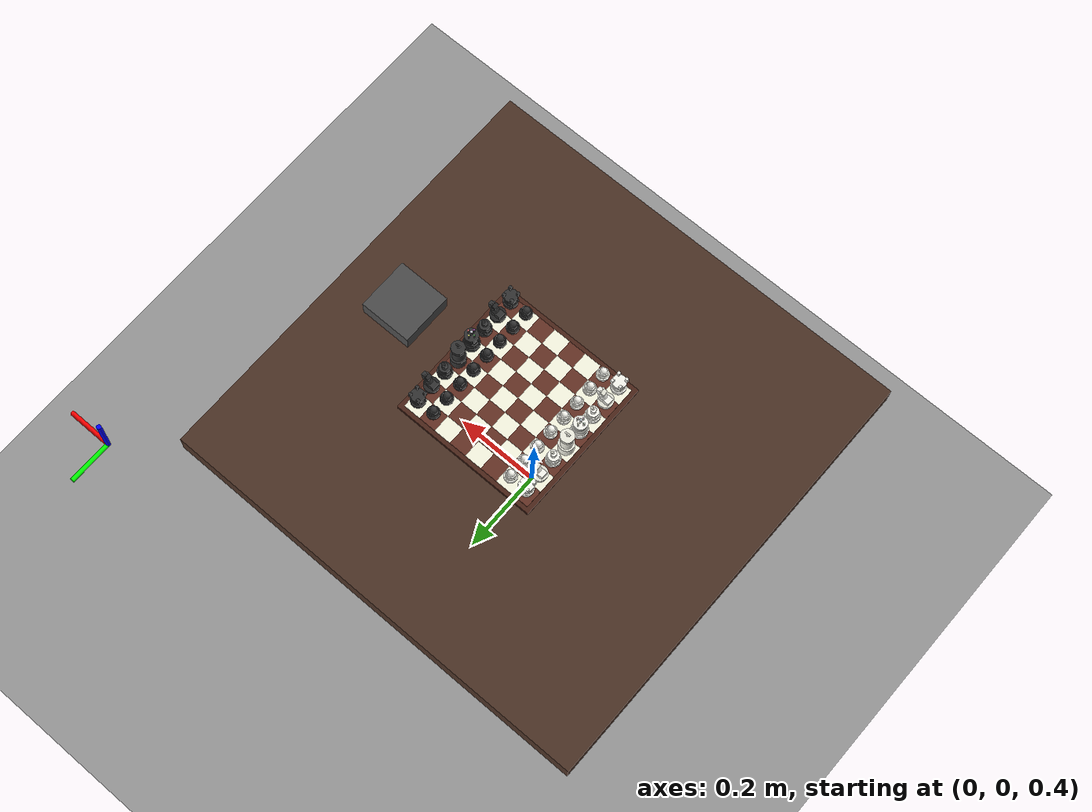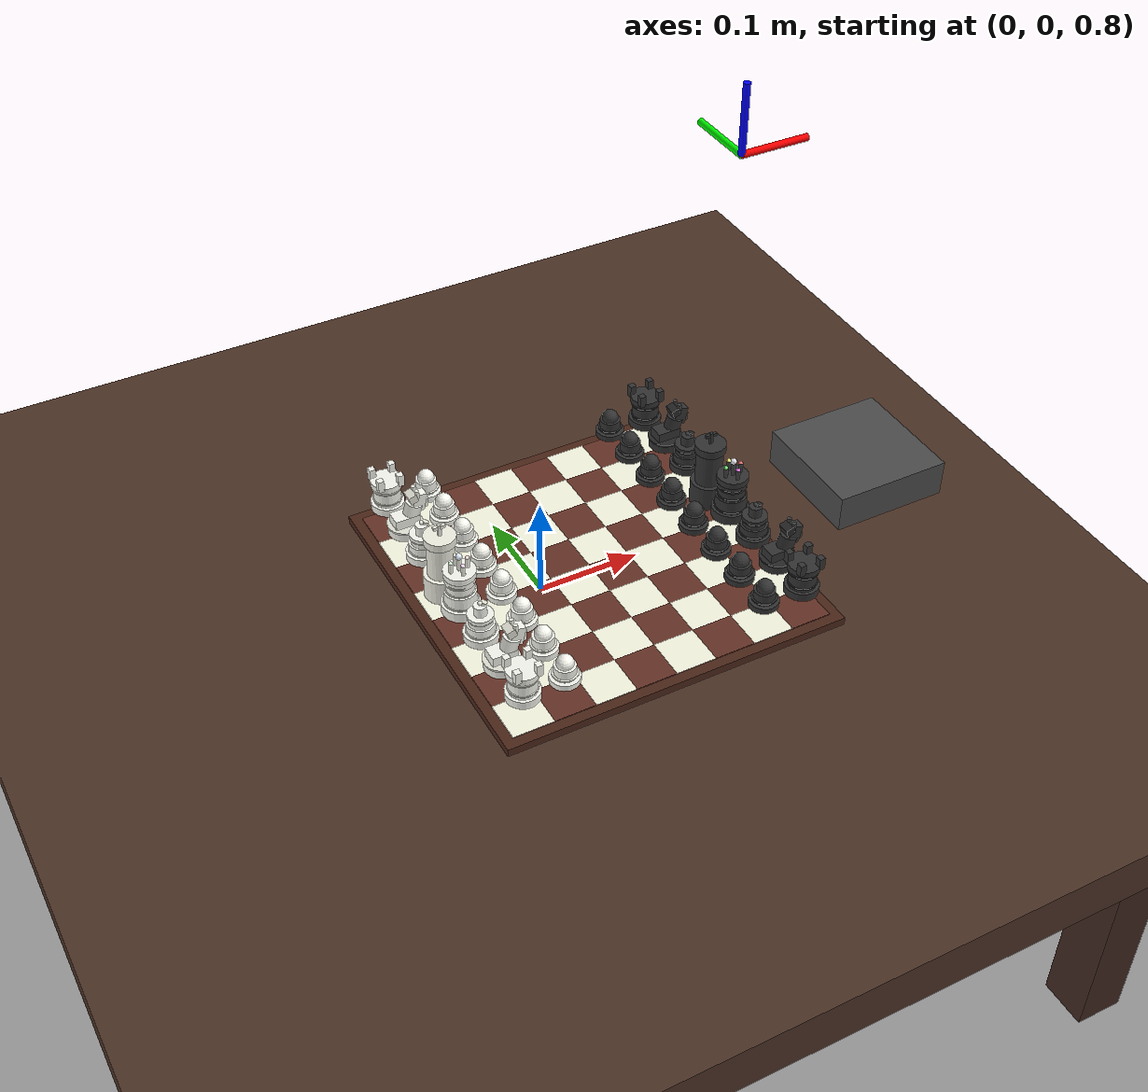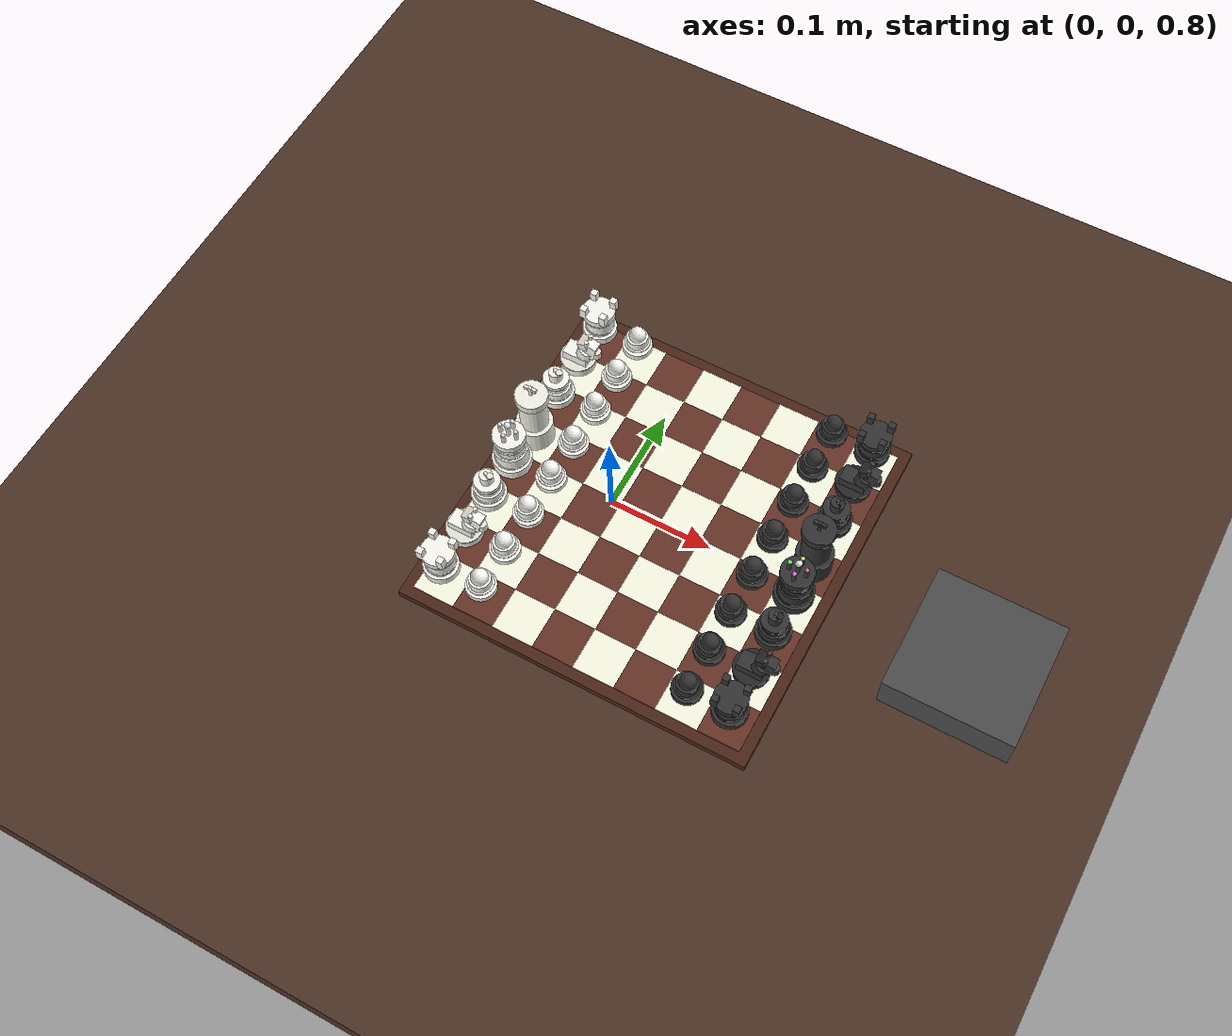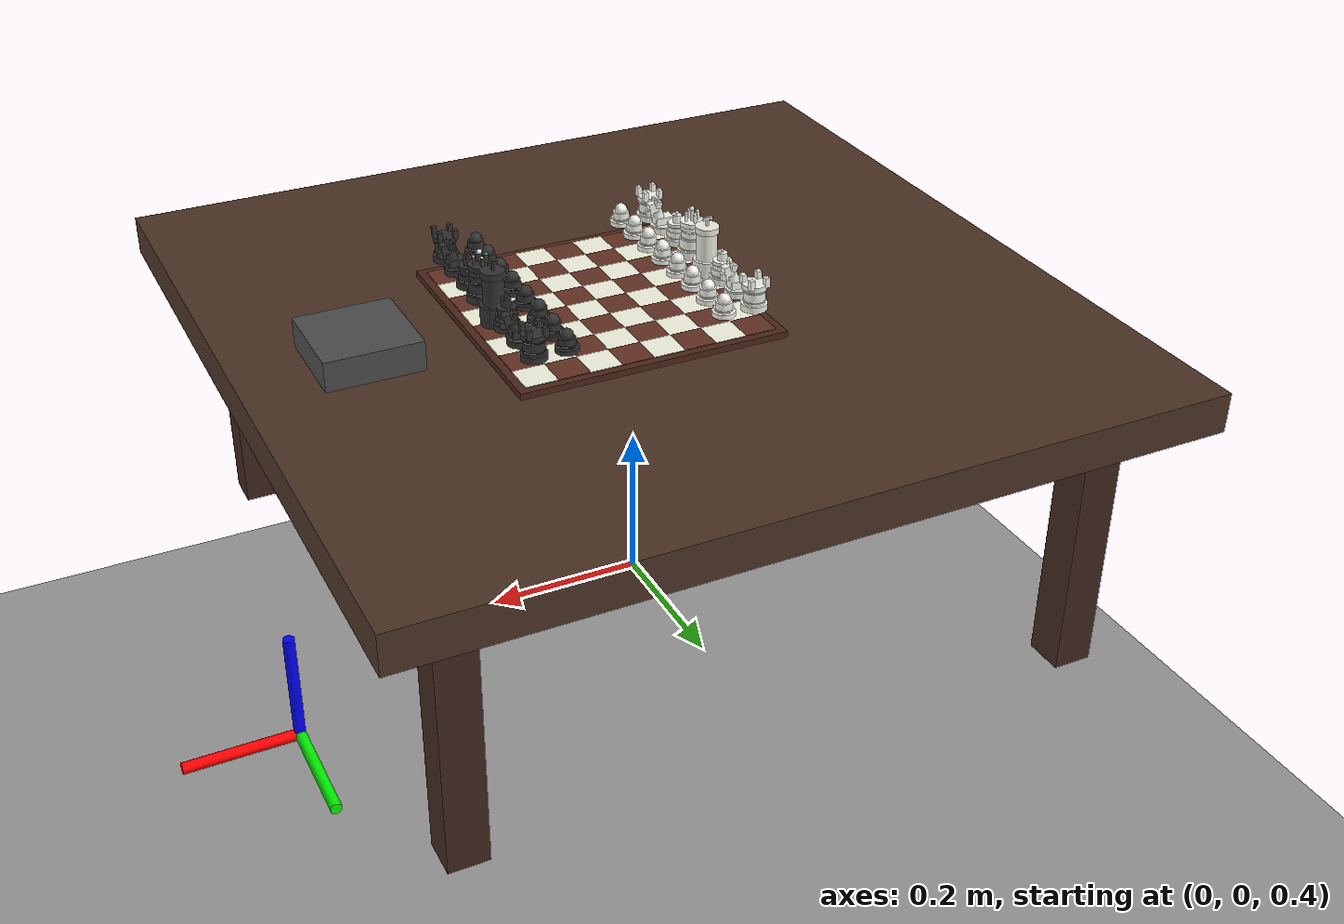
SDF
<?xml version="1.0" ?>
<sdf version="1.6">
  <world name="chess_table_world">

    <!-- Physics settings optimized for robotic manipulation -->
    <physics name="default_physics" default="0" type="ode">
      <gravity>0 0 -9.8066</gravity>
      <ode>
        <solver>
          <type>quick</type>
          <iters>200</iters>
          <sor>1.3</sor>
        </solver>
        <constraints>
          <cfm>0.00001</cfm>
          <erp>0.2</erp>
          <contact_max_correcting_vel>100</contact_max_correcting_vel>
          <contact_surface_layer>0.001</contact_surface_layer>
        </constraints>
      </ode>
      <max_step_size>0.001</max_step_size>
      <real_time_factor>1</real_time_factor>
      <real_time_update_rate>1000</real_time_update_rate>
    </physics>

    <!-- Scene settings -->
    <scene>
      <ambient>0.6 0.6 0.6</ambient>
      <background>0.8 0.8 0.9</background>
      <shadows>true</shadows>
    </scene>

    <!-- Sun light -->
    <light type="directional" name="sun">
      <cast_shadows>true</cast_shadows>
      <pose>0 0 10 0 0 0</pose>
      <diffuse>1.0 1.0 1.0 1</diffuse>
      <specular>0.2 0.2 0.2 1</specular>
      <attenuation>
        <range>1000</range>
        <constant>0.9</constant>
        <linear>0.01</linear>
        <quadratic>0.001</quadratic>
      </attenuation>
      <direction>-0.5 0.1 -0.9</direction>
    </light>

    <!-- Additional task lighting for precise work -->
    <light type="point" name="task_light_1">
      <pose>0.5 0.5 2.0 0 0 0</pose>
      <diffuse>0.8 0.8 0.8 1</diffuse>
      <specular>0.2 0.2 0.2 1</specular>
      <attenuation>
        <range>10</range>
        <constant>0.8</constant>
        <linear>0.01</linear>
        <quadratic>0.001</quadratic>
      </attenuation>
    </light>

    <light type="point" name="task_light_2">
      <pose>-0.5 -0.5 2.0 0 0 0</pose>
      <diffuse>0.8 0.8 0.8 1</diffuse>
      <specular>0.2 0.2 0.2 1</specular>
      <attenuation>
        <range>10</range>
        <constant>0.8</constant>
        <linear>0.01</linear>
        <quadratic>0.001</quadratic>
      </attenuation>
    </light>

    <!-- Ground plane -->
    <model name="ground_plane">
      <static>true</static>
      <link name="link">
        <collision name="collision">
          <geometry>
            <plane>
              <normal>0 0 1</normal>
              <size>20 20</size>
            </plane>
          </geometry>
          <surface>
            <friction>
              <ode>
                <mu>1.0</mu>
                <mu2>1.0</mu2>
              </ode>
            </friction>
          </surface>
        </collision>
        <visual name="visual">
          <geometry>
            <plane>
              <normal>0 0 1</normal>
              <size>20 20</size>
            </plane>
          </geometry>
          <material>
            <ambient>0.5 0.5 0.5 1</ambient>
            <diffuse>0.6 0.6 0.6 1</diffuse>
            <specular>0.1 0.1 0.1 1</specular>
          </material>
        </visual>
      </link>
    </model>

    <!-- Chess/Work Table -->
    <model name="chess_table_with_mount">
      <static>true</static>
      <pose>0 0 0.4 0 0 0</pose>

      <!-- Table top -->
      <link name="table_top">
        <pose>0 0 0.375 0 0 0</pose>
        <collision name="top_collision">
          <geometry>
            <box>
              <size>1.0 1.0 0.05</size>
            </box>
          </geometry>
          <surface>
            <friction>
              <ode>
                <mu>0.8</mu>
                <mu2>0.8</mu2>
              </ode>
            </friction>
          </surface>
        </collision>
        <visual name="top_visual">
          <geometry>
            <box>
              <size>1.0 1.0 0.05</size>
            </box>
          </geometry>
          <material>
            <ambient>0.2 0.15 0.1 1</ambient>
            <diffuse>0.3 0.2 0.15 1</diffuse>
            <specular>0.1 0.05 0.02 1</specular>
          </material>
        </visual>
      </link>

      <!-- Robot mounting platform - positioned for optimal reach -->
      <link name="robot_mount_platform">
        <!-- Position optimized for chess board reach -->
        <pose>0.35 0.0 0.4025 0 0 0</pose>

        <!-- Base mounting plate -->
        <collision name="mount_base_collision">
          <geometry>
            <box>
              <size>0.12 0.12 0.01</size>
            </box>
          </geometry>
          <surface>
            <friction>
              <ode>
                <mu>10.0</mu>
                <mu2>10.0</mu2>
              </ode>
            </friction>
            <contact>
              <ode>
                <soft_cfm>0.00001</soft_cfm>
                <soft_erp>0.2</soft_erp>
                <kp>10000000</kp>
                <kd>1000</kd>
                <max_vel>0.001</max_vel>
                <min_depth>0.0001</min_depth>
              </ode>
            </contact>
          </surface>
        </collision>
        <visual name="mount_base_visual">
          <pose>0 0 0.01 0 0 0</pose>  <!-- Offset downward to extend above -->
          <geometry>
            <box>
              <size>0.12 0.12 0.05</size>
            </box>
          </geometry>
          <material>
            <ambient>0.2 0.2 0.2 1</ambient>
            <diffuse>0.3 0.3 0.3 1</diffuse>
            <specular>0.1 0.1 0.1 1</specular>
          </material>
        </visual>

        <!-- Mounting holes representation -->
        <visual name="mount_hole_1">
          <pose>0.04 0.04 0.0025 0 0 0</pose>
          <geometry>
            <cylinder>
              <radius>0.003</radius>
              <length>0.005</length>
            </cylinder>
          </geometry>
          <material>
            <ambient>0.1 0.1 0.1 1</ambient>
            <diffuse>0.1 0.1 0.1 1</diffuse>
          </material>
        </visual>

        <visual name="mount_hole_2">
          <pose>-0.04 0.04 0.0025 0 0 0</pose>
          <geometry>
            <cylinder>
              <radius>0.003</radius>
              <length>0.005</length>
            </cylinder>
          </geometry>
          <material>
            <ambient>0.1 0.1 0.1 1</ambient>
            <diffuse>0.1 0.1 0.1 1</diffuse>
          </material>
        </visual>

        <visual name="mount_hole_3">
          <pose>0.04 -0.04 0.0025 0 0 0</pose>
          <geometry>
            <cylinder>
              <radius>0.003</radius>
              <length>0.005</length>
            </cylinder>
          </geometry>
          <material>
            <ambient>0.1 0.1 0.1 1</ambient>
            <diffuse>0.1 0.1 0.1 1</diffuse>
          </material>
        </visual>

        <visual name="mount_hole_4">
          <pose>-0.04 -0.04 0.0025 0 0 0</pose>
          <geometry>
            <cylinder>
              <radius>0.003</radius>
              <length>0.005</length>
            </cylinder>
          </geometry>
          <material>
            <ambient>0.1 0.1 0.1 1</ambient>
            <diffuse>0.1 0.1 0.1 1</diffuse>
          </material>
        </visual>
      </link>

      <!-- Table legs -->
      <link name="leg_1">
        <pose>0.4 0.4 0.175 0 0 0</pose>
        <collision name="leg1_collision">
          <geometry>
            <box>
              <size>0.05 0.05 0.35</size>
            </box>
          </geometry>
        </collision>
        <visual name="leg1_visual">
          <geometry>
            <box>
              <size>0.05 0.05 0.35</size>
            </box>
          </geometry>
          <material>
            <ambient>0.15 0.1 0.08 1</ambient>
            <diffuse>0.25 0.15 0.12 1</diffuse>
          </material>
        </visual>
      </link>

      <link name="leg_2">
        <pose>-0.4 0.4 0.175 0 0 0</pose>
        <collision name="leg2_collision">
          <geometry>
            <box>
              <size>0.05 0.05 0.35</size>
            </box>
          </geometry>
        </collision>
        <visual name="leg2_visual">
          <geometry>
            <box>
              <size>0.05 0.05 0.35</size>
            </box>
          </geometry>
          <material>
            <ambient>0.15 0.1 0.08 1</ambient>
            <diffuse>0.25 0.15 0.12 1</diffuse>
          </material>
        </visual>
      </link>

      <link name="leg_3">
        <pose>0.4 -0.4 0.175 0 0 0</pose>
        <collision name="leg3_collision">
          <geometry>
            <box>
              <size>0.05 0.05 0.35</size>
            </box>
          </geometry>
        </collision>
        <visual name="leg3_visual">
          <geometry>
            <box>
              <size>0.05 0.05 0.35</size>
            </box>
          </geometry>
          <material>
            <ambient>0.15 0.1 0.08 1</ambient>
            <diffuse>0.25 0.15 0.12 1</diffuse>
          </material>
        </visual>
      </link>

      <link name="leg_4">
        <pose>-0.4 -0.4 0.175 0 0 0</pose>
        <collision name="leg4_collision">
          <geometry>
            <box>
              <size>0.05 0.05 0.35</size>
            </box>
          </geometry>
        </collision>
        <visual name="leg4_visual">
          <geometry>
            <box>
              <size>0.05 0.05 0.35</size>
            </box>
          </geometry>
          <material>
            <ambient>0.15 0.1 0.08 1</ambient>
            <diffuse>0.25 0.15 0.12 1</diffuse>
          </material>
        </visual>
      </link>

      <!-- Fixed joints to connect everything -->
      <joint name="leg1_joint" type="fixed">
        <parent>table_top</parent>
        <child>leg_1</child>
      </joint>
      <joint name="leg2_joint" type="fixed">
        <parent>table_top</parent>
        <child>leg_2</child>
      </joint>
      <joint name="leg3_joint" type="fixed">
        <parent>table_top</parent>
        <child>leg_3</child>
      </joint>
      <joint name="leg4_joint" type="fixed">
        <parent>table_top</parent>
        <child>leg_4</child>
      </joint>
      <joint name="mount_joint" type="fixed">
        <parent>table_top</parent>
        <child>robot_mount_platform</child>
      </joint>
    </model>

    <!-- Chess Board -->
    <model name="chess_board">
      <static>true</static>
      <pose>0.05 0 0.8005 0 0 0</pose>

      <!-- Board frame -->
      <link name="board_frame">
        <collision name="frame_collision">
          <geometry>
            <box>
              <size>0.34 0.34 0.015</size>
            </box>
          </geometry>
        </collision>
        <visual name="frame_visual">
          <geometry>
            <box>
              <size>0.34 0.34 0.015</size>
            </box>
          </geometry>
          <material>
            <ambient>0.2 0.1 0.05 1</ambient>
            <diffuse>0.3 0.15 0.1 1</diffuse>
            <specular>0.2 0.1 0.05 1</specular>
          </material>
        </visual>
      </link>

      <!-- Rank 1 (a1-h1) -->
      <link name="square_a1">
        <pose>-0.140 -0.140 0.008 0 0 0</pose>
        <visual name="a1_visual">
          <geometry><box><size>0.04 0.04 0.001</size></box></geometry>
          <material><ambient>0.95 0.95 0.85 1</ambient><diffuse>0.98 0.98 0.9 1</diffuse><specular>0.1 0.1 0.1 1</specular></material>
        </visual>
      </link>
      <link name="square_b1">
        <pose>-0.140 -0.100 0.008 0 0 0</pose>
        <visual name="b1_visual">
          <geometry><box><size>0.04 0.04 0.001</size></box></geometry>
          <material><ambient>0.3 0.15 0.1 1</ambient><diffuse>0.4 0.2 0.15 1</diffuse><specular>0.1 0.1 0.1 1</specular></material>
        </visual>
      </link>
      <link name="square_c1">
        <pose>-0.140 -0.060 0.008 0 0 0</pose>
        <visual name="c1_visual">
          <geometry><box><size>0.04 0.04 0.001</size></box></geometry>
          <material><ambient>0.95 0.95 0.85 1</ambient><diffuse>0.98 0.98 0.9 1</diffuse><specular>0.1 0.1 0.1 1</specular></material>
        </visual>
      </link>
      <link name="square_d1">
        <pose>-0.140 -0.020 0.008 0 0 0</pose>
        <visual name="d1_visual">
          <geometry><box><size>0.04 0.04 0.001</size></box></geometry>
          <material><ambient>0.3 0.15 0.1 1</ambient><diffuse>0.4 0.2 0.15 1</diffuse><specular>0.1 0.1 0.1 1</specular></material>
        </visual>
      </link>
      <link name="square_e1">
        <pose>-0.140 0.020 0.008 0 0 0</pose>
        <visual name="e1_visual">
          <geometry><box><size>0.04 0.04 0.001</size></box></geometry>
          <material><ambient>0.95 0.95 0.85 1</ambient><diffuse>0.98 0.98 0.9 1</diffuse><specular>0.1 0.1 0.1 1</specular></material>
        </visual>
      </link>
      <link name="square_f1">
        <pose>-0.140 0.060 0.008 0 0 0</pose>
        <visual name="f1_visual">
          <geometry><box><size>0.04 0.04 0.001</size></box></geometry>
          <material><ambient>0.3 0.15 0.1 1</ambient><diffuse>0.4 0.2 0.15 1</diffuse><specular>0.1 0.1 0.1 1</specular></material>
        </visual>
      </link>
      <link name="square_g1">
        <pose>-0.140 0.100 0.008 0 0 0</pose>
        <visual name="g1_visual">
          <geometry><box><size>0.04 0.04 0.001</size></box></geometry>
          <material><ambient>0.95 0.95 0.85 1</ambient><diffuse>0.98 0.98 0.9 1</diffuse><specular>0.1 0.1 0.1 1</specular></material>
        </visual>
      </link>
      <link name="square_h1">
        <pose>-0.140 0.140 0.008 0 0 0</pose>
        <visual name="h1_visual">
          <geometry><box><size>0.04 0.04 0.001</size></box></geometry>
          <material><ambient>0.3 0.15 0.1 1</ambient><diffuse>0.4 0.2 0.15 1</diffuse><specular>0.1 0.1 0.1 1</specular></material>
        </visual>
      </link>

      <!-- Rank 2 (a2-h2) -->
      <link name="square_a2">
        <pose>-0.100 -0.140 0.008 0 0 0</pose>
        <visual name="a2_visual">
          <geometry><box><size>0.04 0.04 0.001</size></box></geometry>
          <material><ambient>0.3 0.15 0.1 1</ambient><diffuse>0.4 0.2 0.15 1</diffuse><specular>0.1 0.1 0.1 1</specular></material>
        </visual>
      </link>
      <link name="square_b2">
        <pose>-0.100 -0.100 0.008 0 0 0</pose>
        <visual name="b2_visual">
          <geometry><box><size>0.04 0.04 0.001</size></box></geometry>
          <material><ambient>0.95 0.95 0.85 1</ambient><diffuse>0.98 0.98 0.9 1</diffuse><specular>0.1 0.1 0.1 1</specular></material>
        </visual>
      </link>
      <link name="square_c2">
        <pose>-0.100 -0.060 0.008 0 0 0</pose>
        <visual name="c2_visual">
          <geometry><box><size>0.04 0.04 0.001</size></box></geometry>
          <material><ambient>0.3 0.15 0.1 1</ambient><diffuse>0.4 0.2 0.15 1</diffuse><specular>0.1 0.1 0.1 1</specular></material>
        </visual>
      </link>
      <link name="square_d2">
        <pose>-0.100 -0.020 0.008 0 0 0</pose>
        <visual name="d2_visual">
          <geometry><box><size>0.04 0.04 0.001</size></box></geometry>
          <material><ambient>0.95 0.95 0.85 1</ambient><diffuse>0.98 0.98 0.9 1</diffuse><specular>0.1 0.1 0.1 1</specular></material>
        </visual>
      </link>
      <link name="square_e2">
        <pose>-0.100 0.020 0.008 0 0 0</pose>
        <visual name="e2_visual">
          <geometry><box><size>0.04 0.04 0.001</size></box></geometry>
          <material><ambient>0.3 0.15 0.1 1</ambient><diffuse>0.4 0.2 0.15 1</diffuse><specular>0.1 0.1 0.1 1</specular></material>
        </visual>
      </link>
      <link name="square_f2">
        <pose>-0.100 0.060 0.008 0 0 0</pose>
        <visual name="f2_visual">
          <geometry><box><size>0.04 0.04 0.001</size></box></geometry>
          <material><ambient>0.95 0.95 0.85 1</ambient><diffuse>0.98 0.98 0.9 1</diffuse><specular>0.1 0.1 0.1 1</specular></material>
        </visual>
      </link>
      <link name="square_g2">
        <pose>-0.100 0.100 0.008 0 0 0</pose>
        <visual name="g2_visual">
          <geometry><box><size>0.04 0.04 0.001</size></box></geometry>
          <material><ambient>0.3 0.15 0.1 1</ambient><diffuse>0.4 0.2 0.15 1</diffuse><specular>0.1 0.1 0.1 1</specular></material>
        </visual>
      </link>
      <link name="square_h2">
        <pose>-0.100 0.140 0.008 0 0 0</pose>
        <visual name="h2_visual">
          <geometry><box><size>0.04 0.04 0.001</size></box></geometry>
          <material><ambient>0.95 0.95 0.85 1</ambient><diffuse>0.98 0.98 0.9 1</diffuse><specular>0.1 0.1 0.1 1</specular></material>
        </visual>
      </link>

      <!-- Rank 3 (a3-h3) -->
      <link name="square_a3">
        <pose>-0.060 -0.140 0.008 0 0 0</pose>
        <visual name="a3_visual">
          <geometry><box><size>0.04 0.04 0.001</size></box></geometry>
          <material><ambient>0.95 0.95 0.85 1</ambient><diffuse>0.98 0.98 0.9 1</diffuse><specular>0.1 0.1 0.1 1</specular></material>
        </visual>
      </link>
      <link name="square_b3">
        <pose>-0.060 -0.100 0.008 0 0 0</pose>
        <visual name="b3_visual">
          <geometry><box><size>0.04 0.04 0.001</size></box></geometry>
          <material><ambient>0.3 0.15 0.1 1</ambient><diffuse>0.4 0.2 0.15 1</diffuse><specular>0.1 0.1 0.1 1</specular></material>
        </visual>
      </link>
      <link name="square_c3">
        <pose>-0.060 -0.060 0.008 0 0 0</pose>
        <visual name="c3_visual">
          <geometry><box><size>0.04 0.04 0.001</size></box></geometry>
          <material><ambient>0.95 0.95 0.85 1</ambient><diffuse>0.98 0.98 0.9 1</diffuse><specular>0.1 0.1 0.1 1</specular></material>
        </visual>
      </link>
      <link name="square_d3">
        <pose>-0.060 -0.020 0.008 0 0 0</pose>
        <visual name="d3_visual">
          <geometry><box><size>0.04 0.04 0.001</size></box></geometry>
          <material><ambient>0.3 0.15 0.1 1</ambient><diffuse>0.4 0.2 0.15 1</diffuse><specular>0.1 0.1 0.1 1</specular></material>
        </visual>
      </link>
      <link name="square_e3">
        <pose>-0.060 0.020 0.008 0 0 0</pose>
        <visual name="e3_visual">
          <geometry><box><size>0.04 0.04 0.001</size></box></geometry>
          <material><ambient>0.95 0.95 0.85 1</ambient><diffuse>0.98 0.98 0.9 1</diffuse><specular>0.1 0.1 0.1 1</specular></material>
        </visual>
      </link>
      <link name="square_f3">
        <pose>-0.060 0.060 0.008 0 0 0</pose>
        <visual name="f3_visual">
          <geometry><box><size>0.04 0.04 0.001</size></box></geometry>
          <material><ambient>0.3 0.15 0.1 1</ambient><diffuse>0.4 0.2 0.15 1</diffuse><specular>0.1 0.1 0.1 1</specular></material>
        </visual>
      </link>
      <link name="square_g3">
        <pose>-0.060 0.100 0.008 0 0 0</pose>
        <visual name="g3_visual">
          <geometry><box><size>0.04 0.04 0.001</size></box></geometry>
          <material><ambient>0.95 0.95 0.85 1</ambient><diffuse>0.98 0.98 0.9 1</diffuse><specular>0.1 0.1 0.1 1</specular></material>
        </visual>
      </link>
      <link name="square_h3">
        <pose>-0.060 0.140 0.008 0 0 0</pose>
        <visual name="h3_visual">
          <geometry><box><size>0.04 0.04 0.001</size></box></geometry>
          <material><ambient>0.3 0.15 0.1 1</ambient><diffuse>0.4 0.2 0.15 1</diffuse><specular>0.1 0.1 0.1 1</specular></material>
        </visual>
      </link>

      <!-- Rank 4 (a4-h4) -->
      <link name="square_a4">
        <pose>-0.020 -0.140 0.008 0 0 0</pose>
        <visual name="a4_visual">
          <geometry><box><size>0.04 0.04 0.001</size></box></geometry>
          <material><ambient>0.3 0.15 0.1 1</ambient><diffuse>0.4 0.2 0.15 1</diffuse><specular>0.1 0.1 0.1 1</specular></material>
        </visual>
      </link>
      <link name="square_b4">
        <pose>-0.020 -0.100 0.008 0 0 0</pose>
        <visual name="b4_visual">
          <geometry><box><size>0.04 0.04 0.001</size></box></geometry>
          <material><ambient>0.95 0.95 0.85 1</ambient><diffuse>0.98 0.98 0.9 1</diffuse><specular>0.1 0.1 0.1 1</specular></material>
        </visual>
      </link>
      <link name="square_c4">
        <pose>-0.020 -0.060 0.008 0 0 0</pose>
        <visual name="c4_visual">
          <geometry><box><size>0.04 0.04 0.001</size></box></geometry>
          <material><ambient>0.3 0.15 0.1 1</ambient><diffuse>0.4 0.2 0.15 1</diffuse><specular>0.1 0.1 0.1 1</specular></material>
        </visual>
      </link>
      <link name="square_d4">
        <pose>-0.020 -0.020 0.008 0 0 0</pose>
        <visual name="d4_visual">
          <geometry><box><size>0.04 0.04 0.001</size></box></geometry>
          <material><ambient>0.95 0.95 0.85 1</ambient><diffuse>0.98 0.98 0.9 1</diffuse><specular>0.1 0.1 0.1 1</specular></material>
        </visual>
      </link>
      <link name="square_e4">
        <pose>-0.020 0.020 0.008 0 0 0</pose>
        <visual name="e4_visual">
          <geometry><box><size>0.04 0.04 0.001</size></box></geometry>
          <material><ambient>0.3 0.15 0.1 1</ambient><diffuse>0.4 0.2 0.15 1</diffuse><specular>0.1 0.1 0.1 1</specular></material>
        </visual>
      </link>
      <link name="square_f4">
        <pose>-0.020 0.060 0.008 0 0 0</pose>
        <visual name="f4_visual">
          <geometry><box><size>0.04 0.04 0.001</size></box></geometry>
          <material><ambient>0.95 0.95 0.85 1</ambient><diffuse>0.98 0.98 0.9 1</diffuse><specular>0.1 0.1 0.1 1</specular></material>
        </visual>
      </link>
      <link name="square_g4">
        <pose>-0.020 0.100 0.008 0 0 0</pose>
        <visual name="g4_visual">
          <geometry><box><size>0.04 0.04 0.001</size></box></geometry>
          <material><ambient>0.3 0.15 0.1 1</ambient><diffuse>0.4 0.2 0.15 1</diffuse><specular>0.1 0.1 0.1 1</specular></material>
        </visual>
      </link>
      <link name="square_h4">
        <pose>-0.020 0.140 0.008 0 0 0</pose>
        <visual name="h4_visual">
          <geometry><box><size>0.04 0.04 0.001</size></box></geometry>
          <material><ambient>0.95 0.95 0.85 1</ambient><diffuse>0.98 0.98 0.9 1</diffuse><specular>0.1 0.1 0.1 1</specular></material>
        </visual>
      </link>

      <!-- Rank 5 (a5-h5) -->
      <link name="square_a5">
        <pose>0.020 -0.140 0.008 0 0 0</pose>
        <visual name="a5_visual">
          <geometry><box><size>0.04 0.04 0.001</size></box></geometry>
          <material><ambient>0.95 0.95 0.85 1</ambient><diffuse>0.98 0.98 0.9 1</diffuse><specular>0.1 0.1 0.1 1</specular></material>
        </visual>
      </link>
      <link name="square_b5">
        <pose>0.020 -0.100 0.008 0 0 0</pose>
        <visual name="b5_visual">
          <geometry><box><size>0.04 0.04 0.001</size></box></geometry>
          <material><ambient>0.3 0.15 0.1 1</ambient><diffuse>0.4 0.2 0.15 1</diffuse><specular>0.1 0.1 0.1 1</specular></material>
        </visual>
      </link>
      <link name="square_c5">
        <pose>0.020 -0.060 0.008 0 0 0</pose>
        <visual name="c5_visual">
          <geometry><box><size>0.04 0.04 0.001</size></box></geometry>
          <material><ambient>0.95 0.95 0.85 1</ambient><diffuse>0.98 0.98 0.9 1</diffuse><specular>0.1 0.1 0.1 1</specular></material>
        </visual>
      </link>
      <link name="square_d5">
        <pose>0.020 -0.020 0.008 0 0 0</pose>
        <visual name="d5_visual">
          <geometry><box><size>0.04 0.04 0.001</size></box></geometry>
          <material><ambient>0.3 0.15 0.1 1</ambient><diffuse>0.4 0.2 0.15 1</diffuse><specular>0.1 0.1 0.1 1</specular></material>
        </visual>
      </link>
      <link name="square_e5">
        <pose>0.020 0.020 0.008 0 0 0</pose>
        <visual name="e5_visual">
          <geometry><box><size>0.04 0.04 0.001</size></box></geometry>
          <material><ambient>0.95 0.95 0.85 1</ambient><diffuse>0.98 0.98 0.9 1</diffuse><specular>0.1 0.1 0.1 1</specular></material>
        </visual>
      </link>
      <link name="square_f5">
        <pose>0.020 0.060 0.008 0 0 0</pose>
        <visual name="f5_visual">
          <geometry><box><size>0.04 0.04 0.001</size></box></geometry>
          <material><ambient>0.3 0.15 0.1 1</ambient><diffuse>0.4 0.2 0.15 1</diffuse><specular>0.1 0.1 0.1 1</specular></material>
        </visual>
      </link>
      <link name="square_g5">
        <pose>0.020 0.100 0.008 0 0 0</pose>
        <visual name="g5_visual">
          <geometry><box><size>0.04 0.04 0.001</size></box></geometry>
          <material><ambient>0.95 0.95 0.85 1</ambient><diffuse>0.98 0.98 0.9 1</diffuse><specular>0.1 0.1 0.1 1</specular></material>
        </visual>
      </link>
      <link name="square_h5">
        <pose>0.020 0.140 0.008 0 0 0</pose>
        <visual name="h5_visual">
          <geometry><box><size>0.04 0.04 0.001</size></box></geometry>
          <material><ambient>0.3 0.15 0.1 1</ambient><diffuse>0.4 0.2 0.15 1</diffuse><specular>0.1 0.1 0.1 1</specular></material>
        </visual>
      </link>

      <!-- Rank 6 (a6-h6) -->
      <link name="square_a6">
        <pose>0.060 -0.140 0.008 0 0 0</pose>
        <visual name="a6_visual">
          <geometry><box><size>0.04 0.04 0.001</size></box></geometry>
          <material><ambient>0.3 0.15 0.1 1</ambient><diffuse>0.4 0.2 0.15 1</diffuse><specular>0.1 0.1 0.1 1</specular></material>
        </visual>
      </link>
      <link name="square_b6">
        <pose>0.060 -0.100 0.008 0 0 0</pose>
        <visual name="b6_visual">
          <geometry><box><size>0.04 0.04 0.001</size></box></geometry>
          <material><ambient>0.95 0.95 0.85 1</ambient><diffuse>0.98 0.98 0.9 1</diffuse><specular>0.1 0.1 0.1 1</specular></material>
        </visual>
      </link>
      <link name="square_c6">
        <pose>0.060 -0.060 0.008 0 0 0</pose>
        <visual name="c6_visual">
          <geometry><box><size>0.04 0.04 0.001</size></box></geometry>
          <material><ambient>0.3 0.15 0.1 1</ambient><diffuse>0.4 0.2 0.15 1</diffuse><specular>0.1 0.1 0.1 1</specular></material>
        </visual>
      </link>
      <link name="square_d6">
        <pose>0.060 -0.020 0.008 0 0 0</pose>
        <visual name="d6_visual">
          <geometry><box><size>0.04 0.04 0.001</size></box></geometry>
          <material><ambient>0.95 0.95 0.85 1</ambient><diffuse>0.98 0.98 0.9 1</diffuse><specular>0.1 0.1 0.1 1</specular></material>
        </visual>
      </link>
      <link name="square_e6">
        <pose>0.060 0.020 0.008 0 0 0</pose>
        <visual name="e6_visual">
          <geometry><box><size>0.04 0.04 0.001</size></box></geometry>
          <material><ambient>0.3 0.15 0.1 1</ambient><diffuse>0.4 0.2 0.15 1</diffuse><specular>0.1 0.1 0.1 1</specular></material>
        </visual>
      </link>
      <link name="square_f6">
        <pose>0.060 0.060 0.008 0 0 0</pose>
        <visual name="f6_visual">
          <geometry><box><size>0.04 0.04 0.001</size></box></geometry>
          <material><ambient>0.95 0.95 0.85 1</ambient><diffuse>0.98 0.98 0.9 1</diffuse><specular>0.1 0.1 0.1 1</specular></material>
        </visual>
      </link>
      <link name="square_g6">
        <pose>0.060 0.100 0.008 0 0 0</pose>
        <visual name="g6_visual">
          <geometry><box><size>0.04 0.04 0.001</size></box></geometry>
          <material><ambient>0.3 0.15 0.1 1</ambient><diffuse>0.4 0.2 0.15 1</diffuse><specular>0.1 0.1 0.1 1</specular></material>
        </visual>
      </link>
      <link name="square_h6">
        <pose>0.060 0.140 0.008 0 0 0</pose>
        <visual name="h6_visual">
          <geometry><box><size>0.04 0.04 0.001</size></box></geometry>
          <material><ambient>0.95 0.95 0.85 1</ambient><diffuse>0.98 0.98 0.9 1</diffuse><specular>0.1 0.1 0.1 1</specular></material>
        </visual>
      </link>

      <!-- Rank 7 (a7-h7) -->
      <link name="square_a7">
        <pose>0.100 -0.140 0.008 0 0 0</pose>
        <visual name="a7_visual">
          <geometry><box><size>0.04 0.04 0.001</size></box></geometry>
          <material><ambient>0.95 0.95 0.85 1</ambient><diffuse>0.98 0.98 0.9 1</diffuse><specular>0.1 0.1 0.1 1</specular></material>
        </visual>
      </link>
      <link name="square_b7">
        <pose>0.100 -0.100 0.008 0 0 0</pose>
        <visual name="b7_visual">
          <geometry><box><size>0.04 0.04 0.001</size></box></geometry>
          <material><ambient>0.3 0.15 0.1 1</ambient><diffuse>0.4 0.2 0.15 1</diffuse><specular>0.1 0.1 0.1 1</specular></material>
        </visual>
      </link>
      <link name="square_c7">
        <pose>0.100 -0.060 0.008 0 0 0</pose>
        <visual name="c7_visual">
          <geometry><box><size>0.04 0.04 0.001</size></box></geometry>
          <material><ambient>0.95 0.95 0.85 1</ambient><diffuse>0.98 0.98 0.9 1</diffuse><specular>0.1 0.1 0.1 1</specular></material>
        </visual>
      </link>
      <link name="square_d7">
        <pose>0.100 -0.020 0.008 0 0 0</pose>
        <visual name="d7_visual">
          <geometry><box><size>0.04 0.04 0.001</size></box></geometry>
          <material><ambient>0.3 0.15 0.1 1</ambient><diffuse>0.4 0.2 0.15 1</diffuse><specular>0.1 0.1 0.1 1</specular></material>
        </visual>
      </link>
      <link name="square_e7">
        <pose>0.100 0.020 0.008 0 0 0</pose>
        <visual name="e7_visual">
          <geometry><box><size>0.04 0.04 0.001</size></box></geometry>
          <material><ambient>0.95 0.95 0.85 1</ambient><diffuse>0.98 0.98 0.9 1</diffuse><specular>0.1 0.1 0.1 1</specular></material>
        </visual>
      </link>
      <link name="square_f7">
        <pose>0.100 0.060 0.008 0 0 0</pose>
        <visual name="f7_visual">
          <geometry><box><size>0.04 0.04 0.001</size></box></geometry>
          <material><ambient>0.3 0.15 0.1 1</ambient><diffuse>0.4 0.2 0.15 1</diffuse><specular>0.1 0.1 0.1 1</specular></material>
        </visual>
      </link>
      <link name="square_g7">
        <pose>0.100 0.100 0.008 0 0 0</pose>
        <visual name="g7_visual">
          <geometry><box><size>0.04 0.04 0.001</size></box></geometry>
          <material><ambient>0.95 0.95 0.85 1</ambient><diffuse>0.98 0.98 0.9 1</diffuse><specular>0.1 0.1 0.1 1</specular></material>
        </visual>
      </link>
      <link name="square_h7">
        <pose>0.100 0.140 0.008 0 0 0</pose>
        <visual name="h7_visual">
          <geometry><box><size>0.04 0.04 0.001</size></box></geometry>
          <material><ambient>0.3 0.15 0.1 1</ambient><diffuse>0.4 0.2 0.15 1</diffuse><specular>0.1 0.1 0.1 1</specular></material>
        </visual>
      </link>

      <!-- Rank 8 (a8-h8) -->
      <link name="square_a8">
        <pose>0.140 -0.140 0.008 0 0 0</pose>
        <visual name="a8_visual">
          <geometry><box><size>0.04 0.04 0.001</size></box></geometry>
          <material><ambient>0.3 0.15 0.1 1</ambient><diffuse>0.4 0.2 0.15 1</diffuse><specular>0.1 0.1 0.1 1</specular></material>
        </visual>
      </link>
      <link name="square_b8">
        <pose>0.140 -0.100 0.008 0 0 0</pose>
        <visual name="b8_visual">
          <geometry><box><size>0.04 0.04 0.001</size></box></geometry>
          <material><ambient>0.95 0.95 0.85 1</ambient><diffuse>0.98 0.98 0.9 1</diffuse><specular>0.1 0.1 0.1 1</specular></material>
        </visual>
      </link>
      <link name="square_c8">
        <pose>0.140 -0.060 0.008 0 0 0</pose>
        <visual name="c8_visual">
          <geometry><box><size>0.04 0.04 0.001</size></box></geometry>
          <material><ambient>0.3 0.15 0.1 1</ambient><diffuse>0.4 0.2 0.15 1</diffuse><specular>0.1 0.1 0.1 1</specular></material>
        </visual>
      </link>
      <link name="square_d8">
        <pose>0.140 -0.020 0.008 0 0 0</pose>
        <visual name="d8_visual">
          <geometry><box><size>0.04 0.04 0.001</size></box></geometry>
          <material><ambient>0.95 0.95 0.85 1</ambient><diffuse>0.98 0.98 0.9 1</diffuse><specular>0.1 0.1 0.1 1</specular></material>
        </visual>
      </link>
      <link name="square_e8">
        <pose>0.140 0.020 0.008 0 0 0</pose>
        <visual name="e8_visual">
          <geometry><box><size>0.04 0.04 0.001</size></box></geometry>
          <material><ambient>0.3 0.15 0.1 1</ambient><diffuse>0.4 0.2 0.15 1</diffuse><specular>0.1 0.1 0.1 1</specular></material>
        </visual>
      </link>
      <link name="square_f8">
        <pose>0.140 0.060 0.008 0 0 0</pose>
        <visual name="f8_visual">
          <geometry><box><size>0.04 0.04 0.001</size></box></geometry>
          <material><ambient>0.95 0.95 0.85 1</ambient><diffuse>0.98 0.98 0.9 1</diffuse><specular>0.1 0.1 0.1 1</specular></material>
        </visual>
      </link>
      <link name="square_g8">
        <pose>0.140 0.100 0.008 0 0 0</pose>
        <visual name="g8_visual">
          <geometry><box><size>0.04 0.04 0.001</size></box></geometry>
          <material><ambient>0.3 0.15 0.1 1</ambient><diffuse>0.4 0.2 0.15 1</diffuse><specular>0.1 0.1 0.1 1</specular></material>
        </visual>
      </link>
      <link name="square_h8">
        <pose>0.140 0.140 0.008 0 0 0</pose>
        <visual name="h8_visual">
          <geometry><box><size>0.04 0.04 0.001</size></box></geometry>
          <material><ambient>0.95 0.95 0.85 1</ambient><diffuse>0.98 0.98 0.9 1</diffuse><specular>0.1 0.1 0.1 1</specular></material>
        </visual>
      </link>
    </model>

    <!-- White Pawns (row 2) -->
    <include>
      <uri>model://chess_pawn_white</uri>
      <pose>-0.05 -0.14 0.8315 0 0 0</pose>
      <name>white_pawn_a2</name>
    </include>
    <include>
      <uri>model://chess_pawn_white</uri>
      <pose>-0.05 -0.10 0.8315 0 0 0</pose>
      <name>white_pawn_b2</name>
    </include>
    <include>
      <uri>model://chess_pawn_white</uri>
      <pose>-0.05 -0.06 0.8315 0 0 0</pose>
      <name>white_pawn_c2</name>
    </include>
    <include>
      <uri>model://chess_pawn_white</uri>
      <pose>-0.05 -0.02 0.8315 0 0 0</pose>
      <name>white_pawn_d2</name>
    </include>
    <include>
      <uri>model://chess_pawn_white</uri>
      <pose>-0.05 0.02 0.8315 0 0 0</pose>
      <name>white_pawn_e2</name>
    </include>
    <include>
      <uri>model://chess_pawn_white</uri>
      <pose>-0.05 0.06 0.8315 0 0 0</pose>
      <name>white_pawn_f2</name>
    </include>
    <include>
      <uri>model://chess_pawn_white</uri>
      <pose>-0.05 0.10 0.8315 0 0 0</pose>
      <name>white_pawn_g2</name>
    </include>
    <include>
      <uri>model://chess_pawn_white</uri>
      <pose>-0.05 0.14 0.8315 0 0 0</pose>
      <name>white_pawn_h2</name>
    </include>

    <!-- White Back Pieces (row 1) -->
    <include>
      <uri>model://chess_rook_white</uri>
      <pose>-0.09 -0.14 0.8315 0 0 0</pose>
      <name>white_rook_a1</name>
    </include>
    <include>
      <uri>model://chess_knight_white</uri>
      <pose>-0.09 -0.10 0.8315 0 0 0</pose>
      <name>white_knight_b1</name>
    </include>
    <include>
      <uri>model://chess_bishop_white</uri>
      <pose>-0.09 -0.06 0.8315 0 0 0</pose>
      <name>white_bishop_c1</name>
    </include>
    <include>
      <uri>model://chess_queen_white</uri>
      <pose>-0.09 -0.02 0.8315 0 0 0</pose>
      <name>white_queen_d1</name>
    </include>
    <include>
      <uri>model://chess_king_white</uri>
      <pose>-0.09 0.02 0.8315 0 0 0</pose>
      <name>white_king_e1</name>
    </include>
    <include>
      <uri>model://chess_bishop_white</uri>
      <pose>-0.09 0.06 0.8315 0 0 0</pose>
      <name>white_bishop_f1</name>
    </include>
    <include>
      <uri>model://chess_knight_white</uri>
      <pose>-0.09 0.10 0.8315 0 0 0</pose>
      <name>white_knight_g1</name>
    </include>
    <include>
      <uri>model://chess_rook_white</uri>
      <pose>-0.09 0.14 0.8315 0 0 0</pose>
      <name>white_rook_h1</name>
    </include>

    <!-- Black Pawns (row 7) -->
    <include>
      <uri>model://chess_pawn_black</uri>
      <pose>0.15 -0.14 0.8315 0 0 0</pose>
      <name>black_pawn_a7</name>
    </include>
    <include>
      <uri>model://chess_pawn_black</uri>
      <pose>0.15 -0.10 0.8315 0 0 0</pose>
      <name>black_pawn_b7</name>
    </include>
    <include>
      <uri>model://chess_pawn_black</uri>
      <pose>0.15 -0.06 0.8315 0 0 0</pose>
      <name>black_pawn_c7</name>
    </include>
    <include>
      <uri>model://chess_pawn_black</uri>
      <pose>0.15 -0.02 0.8315 0 0 0</pose>
      <name>black_pawn_d7</name>
    </include>
    <include>
      <uri>model://chess_pawn_black</uri>
      <pose>0.15 0.02 0.8315 0 0 0</pose>
      <name>black_pawn_e7</name>
    </include>
    <include>
      <uri>model://chess_pawn_black</uri>
      <pose>0.15 0.06 0.8315 0 0 0</pose>
      <name>black_pawn_f7</name>
    </include>
    <include>
      <uri>model://chess_pawn_black</uri>
      <pose>0.15 0.10 0.8315 0 0 0</pose>
      <name>black_pawn_g7</name>
    </include>
    <include>
      <uri>model://chess_pawn_black</uri>
      <pose>0.15 0.14 0.8315 0 0 0</pose>
      <name>black_pawn_h7</name>
    </include>

    <!-- Black Back Pieces (row 8) -->
    <include>
      <uri>model://chess_rook_black</uri>
      <pose>0.19 -0.14 0.8315 0 0 0</pose>
      <name>black_rook_a8</name>
    </include>
    <include>
      <uri>model://chess_knight_black</uri>
      <pose>0.19 -0.10 0.8315 0 0 0</pose>
      <name>black_knight_b8</name>
    </include>
    <include>
      <uri>model://chess_bishop_black</uri>
      <pose>0.19 -0.06 0.8315 0 0 0</pose>
      <name>black_bishop_c8</name>
    </include>
    <include>
      <uri>model://chess_queen_black</uri>
      <pose>0.19 -0.02 0.8315 0 0 0</pose>
      <name>black_queen_d8</name>
    </include>
    <include>
      <uri>model://chess_king_black</uri>
      <pose>0.19 0.02 0.8315 0 0 0</pose>
      <name>black_king_e8</name>
    </include>
    <include>
      <uri>model://chess_bishop_black</uri>
      <pose>0.19 0.06 0.8315 0 0 0</pose>
      <name>black_bishop_f8</name>
    </include>
    <include>
      <uri>model://chess_knight_black</uri>
      <pose>0.19 0.10 0.8315 0 0 0</pose>
      <name>black_knight_g8</name>
    </include>
    <include>
      <uri>model://chess_rook_black</uri>
      <pose>0.19 0.14 0.8315 0 0 0</pose>
      <name>black_rook_h8</name>
    </include>

    <!-- Coordinate frame markers -->
    <model name="coordinate_markers">
      <static>true</static>
      <pose>0.6 0.6 0.8 0 0 0</pose>

      <link name="x_axis">
        <visual name="x_visual">
          <geometry>
            <cylinder>
              <radius>0.005</radius>
              <length>0.1</length>
            </cylinder>
          </geometry>
          <pose>0.05 0 0 0 1.5708 0</pose>
          <material>
            <ambient>1 0 0 1</ambient>
            <diffuse>1 0 0 1</diffuse>
          </material>
        </visual>
      </link>

      <link name="y_axis">
        <visual name="y_visual">
          <geometry>
            <cylinder>
              <radius>0.005</radius>
              <length>0.1</length>
            </cylinder>
          </geometry>
          <pose>0 0.05 0 -1.5708 0 0</pose>
          <material>
            <ambient>0 1 0 1</ambient>
            <diffuse>0 1 0 1</diffuse>
          </material>
        </visual>
      </link>

      <link name="z_axis">
        <visual name="z_visual">
          <geometry>
            <cylinder>
              <radius>0.005</radius>
              <length>0.1</length>
            </cylinder>
          </geometry>
          <pose>0 0 0.05 0 0 0</pose>
          <material>
            <ambient>0 0 1 1</ambient>
            <diffuse>0 0 1 1</diffuse>
          </material>
        </visual>
      </link>
    </model>

  </world>
</sdf>

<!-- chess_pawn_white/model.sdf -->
<sdf version="1.6">
  <model name="chess_pawn_white">
    <link name="link">
      <pose>0 0 0 0 0 0</pose>

      <inertial>
        <mass>0.05</mass>
        <pose>0 0 0.012 0 0 0</pose>
        <inertia>
          <ixx>0.00001</ixx>
          <ixy>0</ixy>
          <ixz>0</ixz>
          <iyy>0.00001</iyy>
          <iyz>0</iyz>
          <izz>0.00001</izz>
        </inertia>
      </inertial>

      <!-- Base platform -->
      <collision name="base_collision">
        <pose>0 0 0.003 0 0 0</pose>
        <geometry>
          <cylinder>
            <radius>0.014</radius>
            <length>0.006</length>
          </cylinder>
        </geometry>
        <surface>
          <friction>
            <ode>
              <mu>0.8</mu>
              <mu2>0.8</mu2>
            </ode>
          </friction>
          <bounce>
            <restitution_coefficient>0.1</restitution_coefficient>
          </bounce>
        </surface>
      </collision>

      <!-- Main body (narrower waist) -->
      <collision name="body_collision">
        <pose>0 0 0.012 0 0 0</pose>
        <geometry>
          <cylinder>
            <radius>0.010</radius>
            <length>0.012</length>
          </cylinder>
        </geometry>
      </collision>

      <!-- Rounded head -->
      <collision name="head_collision">
        <pose>0 0 0.020 0 0 0</pose>
        <geometry>
          <sphere>
            <radius>0.008</radius>
          </sphere>
        </geometry>
      </collision>

      <!-- Visuals for detailed appearance -->
      <visual name="base_visual">
        <pose>0 0 0.003 0 0 0</pose>
        <geometry>
          <cylinder>
            <radius>0.014</radius>
            <length>0.006</length>
          </cylinder>
        </geometry>
        <material>
          <ambient>0.95 0.95 0.9 1</ambient>
          <diffuse>0.98 0.98 0.95 1</diffuse>
          <specular>0.4 0.4 0.4 1</specular>
        </material>
      </visual>

      <visual name="body_visual">
        <pose>0 0 0.012 0 0 0</pose>
        <geometry>
          <cylinder>
            <radius>0.010</radius>
            <length>0.012</length>
          </cylinder>
        </geometry>
        <material>
          <ambient>0.95 0.95 0.9 1</ambient>
          <diffuse>0.98 0.98 0.95 1</diffuse>
          <specular>0.4 0.4 0.4 1</specular>
        </material>
      </visual>

      <visual name="head_visual">
        <pose>0 0 0.020 0 0 0</pose>
        <geometry>
          <sphere>
            <radius>0.008</radius>
          </sphere>
        </geometry>
        <material>
          <ambient>0.95 0.95 0.9 1</ambient>
          <diffuse>0.98 0.98 0.95 1</diffuse>
          <specular>0.5 0.5 0.5 1</specular>
        </material>
      </visual>

      <!-- Decorative ring for visual distinction -->
      <visual name="ring_visual">
        <pose>0 0 0.009 0 0 0</pose>
        <geometry>
          <cylinder>
            <radius>0.012</radius>
            <length>0.001</length>
          </cylinder>
        </geometry>
        <material>
          <ambient>0.85 0.85 0.8 1</ambient>
          <diffuse>0.9 0.9 0.85 1</diffuse>
          <specular>0.3 0.3 0.3 1</specular>
        </material>
      </visual>
    </link>
  </model>
</sdf>

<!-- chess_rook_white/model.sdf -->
<sdf version="1.6">
  <model name="chess_rook_white">
    <link name="link">
      <pose>0 0 0 0 0 0</pose>

      <inertial>
        <mass>0.08</mass>
        <pose>0 0 0.015 0 0 0</pose>
        <inertia>
          <ixx>0.00002</ixx>
          <ixy>0</ixy>
          <ixz>0</ixz>
          <iyy>0.00002</iyy>
          <iyz>0</iyz>
          <izz>0.00001</izz>
        </inertia>
      </inertial>

      <!-- Base -->
      <collision name="base_collision">
        <pose>0 0 0.004 0 0 0</pose>
        <geometry>
          <cylinder>
            <radius>0.016</radius>
            <length>0.008</length>
          </cylinder>
        </geometry>
        <surface>
          <friction>
            <ode>
              <mu>0.8</mu>
              <mu2>0.8</mu2>
            </ode>
          </friction>
          <bounce>
            <restitution_coefficient>0.1</restitution_coefficient>
          </bounce>
        </surface>
      </collision>

      <!-- Main tower body -->
      <collision name="tower_collision">
        <pose>0 0 0.018 0 0 0</pose>
        <geometry>
          <cylinder>
            <radius>0.013</radius>
            <length>0.020</length>
          </cylinder>
        </geometry>
      </collision>

      <!-- Castle top (battlements base) -->
      <collision name="castle_base_collision">
        <pose>0 0 0.030 0 0 0</pose>
        <geometry>
          <cylinder>
            <radius>0.015</radius>
            <length>0.006</length>
          </cylinder>
        </geometry>
      </collision>

      <!-- Battlements (4 corner towers) -->
      <collision name="battlement_1">
        <pose>0.010 0.010 0.036 0 0 0</pose>
        <geometry>
          <box>
            <size>0.006 0.006 0.012</size>
          </box>
        </geometry>
      </collision>

      <collision name="battlement_2">
        <pose>-0.010 0.010 0.036 0 0 0</pose>
        <geometry>
          <box>
            <size>0.006 0.006 0.012</size>
          </box>
        </geometry>
      </collision>

      <collision name="battlement_3">
        <pose>0.010 -0.010 0.036 0 0 0</pose>
        <geometry>
          <box>
            <size>0.006 0.006 0.012</size>
          </box>
        </geometry>
      </collision>

      <collision name="battlement_4">
        <pose>-0.010 -0.010 0.036 0 0 0</pose>
        <geometry>
          <box>
            <size>0.006 0.006 0.012</size>
          </box>
        </geometry>
      </collision>

      <!-- Visuals -->
      <visual name="base_visual">
        <pose>0 0 0.004 0 0 0</pose>
        <geometry>
          <cylinder>
            <radius>0.016</radius>
            <length>0.008</length>
          </cylinder>
        </geometry>
        <material>
          <ambient>0.95 0.95 0.9 1</ambient>
          <diffuse>0.98 0.98 0.95 1</diffuse>
          <specular>0.4 0.4 0.4 1</specular>
        </material>
      </visual>

      <visual name="tower_visual">
        <pose>0 0 0.018 0 0 0</pose>
        <geometry>
          <cylinder>
            <radius>0.013</radius>
            <length>0.020</length>
          </cylinder>
        </geometry>
        <material>
          <ambient>0.95 0.95 0.9 1</ambient>
          <diffuse>0.98 0.98 0.95 1</diffuse>
          <specular>0.4 0.4 0.4 1</specular>
        </material>
      </visual>

      <visual name="castle_base_visual">
        <pose>0 0 0.030 0 0 0</pose>
        <geometry>
          <cylinder>
            <radius>0.015</radius>
            <length>0.006</length>
          </cylinder>
        </geometry>
        <material>
          <ambient>0.95 0.95 0.9 1</ambient>
          <diffuse>0.98 0.98 0.95 1</diffuse>
          <specular>0.4 0.4 0.4 1</specular>
        </material>
      </visual>

      <!-- Battlement visuals -->
      <visual name="battlement_1_visual">
        <pose>0.010 0.010 0.036 0 0 0</pose>
        <geometry>
          <box>
            <size>0.006 0.006 0.012</size>
          </box>
        </geometry>
        <material>
          <ambient>0.95 0.95 0.9 1</ambient>
          <diffuse>0.98 0.98 0.95 1</diffuse>
          <specular>0.4 0.4 0.4 1</specular>
        </material>
      </visual>

      <visual name="battlement_2_visual">
        <pose>-0.010 0.010 0.036 0 0 0</pose>
        <geometry>
          <box>
            <size>0.006 0.006 0.012</size>
          </box>
        </geometry>
        <material>
          <ambient>0.95 0.95 0.9 1</ambient>
          <diffuse>0.98 0.98 0.95 1</diffuse>
          <specular>0.4 0.4 0.4 1</specular>
        </material>
      </visual>

      <visual name="battlement_3_visual">
        <pose>0.010 -0.010 0.036 0 0 0</pose>
        <geometry>
          <box>
            <size>0.006 0.006 0.012</size>
          </box>
        </geometry>
        <material>
          <ambient>0.95 0.95 0.9 1</ambient>
          <diffuse>0.98 0.98 0.95 1</diffuse>
          <specular>0.4 0.4 0.4 1</specular>
        </material>
      </visual>

      <visual name="battlement_4_visual">
        <pose>-0.010 -0.010 0.036 0 0 0</pose>
        <geometry>
          <box>
            <size>0.006 0.006 0.012</size>
          </box>
        </geometry>
        <material>
          <ambient>0.95 0.95 0.9 1</ambient>
          <diffuse>0.98 0.98 0.95 1</diffuse>
          <specular>0.4 0.4 0.4 1</specular>
        </material>
      </visual>

      <!-- Decorative bands -->
      <visual name="band_1">
        <pose>0 0 0.012 0 0 0</pose>
        <geometry>
          <cylinder>
            <radius>0.014</radius>
            <length>0.001</length>
          </cylinder>
        </geometry>
        <material>
          <ambient>0.85 0.85 0.8 1</ambient>
          <diffuse>0.9 0.9 0.85 1</diffuse>
          <specular>0.3 0.3 0.3 1</specular>
        </material>
      </visual>

      <visual name="band_2">
        <pose>0 0 0.024 0 0 0</pose>
        <geometry>
          <cylinder>
            <radius>0.014</radius>
            <length>0.001</length>
          </cylinder>
        </geometry>
        <material>
          <ambient>0.85 0.85 0.8 1</ambient>
          <diffuse>0.9 0.9 0.85 1</diffuse>
          <specular>0.3 0.3 0.3 1</specular>
        </material>
      </visual>
    </link>
  </model>
</sdf>

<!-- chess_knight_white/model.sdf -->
<sdf version="1.6">
  <model name="chess_knight_white">
    <link name="link">
      <pose>0 0 0 0 0 0</pose>

      <inertial>
        <mass>0.08</mass>
        <pose>0 0 0.020 0 0 0</pose>
        <inertia>
          <ixx>0.00003</ixx>
          <ixy>0</ixy>
          <ixz>0</ixz>
          <iyy>0.00003</iyy>
          <iyz>0</iyz>
          <izz>0.00001</izz>
        </inertia>
      </inertial>

      <!-- Base platform (horse body) -->
      <collision name="base_collision">
        <pose>0 0 0.004 0 0 0</pose>
        <geometry>
          <cylinder>
            <radius>0.016</radius>
            <length>0.008</length>
          </cylinder>
        </geometry>
        <surface>
          <friction>
            <ode>
              <mu>0.8</mu>
              <mu2>0.8</mu2>
            </ode>
          </friction>
          <bounce>
            <restitution_coefficient>0.1</restitution_coefficient>
          </bounce>
        </surface>
      </collision>

      <!-- Horse body/neck (elongated) -->
      <collision name="body_collision">
        <pose>0 0 0.014 0 0 0</pose>
        <geometry>
          <box>
            <size>0.024 0.016 0.012</size>  <!-- Rectangular horse body -->
          </box>
        </geometry>
      </collision>

      <!-- Horse neck -->
      <collision name="neck_collision">
        <pose>0.008 0 0.022 0 0.3 0</pose>  <!-- Angled forward -->
        <geometry>
          <cylinder>
            <radius>0.008</radius>
            <length>0.016</length>
          </cylinder>
        </geometry>
      </collision>

      <!-- Horse head -->
      <collision name="head_collision">
        <pose>0.014 0 0.032 0 0.2 0</pose>  <!-- Angled horse head -->
        <geometry>
          <box>
            <size>0.012 0.010 0.018</size>  <!-- Horse head shape -->
          </box>
        </geometry>
      </collision>

      <!-- Horse muzzle -->
      <collision name="muzzle_collision">
        <pose>0.020 0 0.028 0 0 0</pose>
        <geometry>
          <cylinder>
            <radius>0.004</radius>
            <length>0.008</length>
          </cylinder>
        </geometry>
      </collision>

      <!-- Horse ears -->
      <collision name="ear_1_collision">
        <pose>0.012 0.004 0.042 0 0 0.5</pose>
        <geometry>
          <cylinder>
            <radius>0.002</radius>
            <length>0.008</length>
          </cylinder>
        </geometry>
      </collision>

      <collision name="ear_2_collision">
        <pose>0.012 -0.004 0.042 0 0 -0.5</pose>
        <geometry>
          <cylinder>
            <radius>0.002</radius>
            <length>0.008</length>
          </cylinder>
        </geometry>
      </collision>

      <!-- Mane -->
      <collision name="mane_collision">
        <pose>0.008 0 0.038 0 -0.3 0</pose>
        <geometry>
          <box>
            <size>0.008 0.012 0.008</size>
          </box>
        </geometry>
      </collision>

      <!-- Visuals -->
      <visual name="base_visual">
        <pose>0 0 0.004 0 0 0</pose>
        <geometry>
          <cylinder>
            <radius>0.016</radius>
            <length>0.008</length>
          </cylinder>
        </geometry>
        <material>
          <ambient>0.95 0.95 0.9 1</ambient>
          <diffuse>0.98 0.98 0.95 1</diffuse>
          <specular>0.4 0.4 0.4 1</specular>
        </material>
      </visual>

      <visual name="body_visual">
        <pose>0 0 0.014 0 0 0</pose>
        <geometry>
          <box>
            <size>0.024 0.016 0.012</size>
          </box>
        </geometry>
        <material>
          <ambient>0.95 0.95 0.9 1</ambient>
          <diffuse>0.98 0.98 0.95 1</diffuse>
          <specular>0.4 0.4 0.4 1</specular>
        </material>
      </visual>

      <visual name="neck_visual">
        <pose>0.008 0 0.022 0 0.3 0</pose>
        <geometry>
          <cylinder>
            <radius>0.008</radius>
            <length>0.016</length>
          </cylinder>
        </geometry>
        <material>
          <ambient>0.95 0.95 0.9 1</ambient>
          <diffuse>0.98 0.98 0.95 1</diffuse>
          <specular>0.4 0.4 0.4 1</specular>
        </material>
      </visual>

      <visual name="head_visual">
        <pose>0.014 0 0.032 0 0.2 0</pose>
        <geometry>
          <box>
            <size>0.012 0.010 0.018</size>
          </box>
        </geometry>
        <material>
          <ambient>0.95 0.95 0.9 1</ambient>
          <diffuse>0.98 0.98 0.95 1</diffuse>
          <specular>0.4 0.4 0.4 1</specular>
        </material>
      </visual>

      <visual name="muzzle_visual">
        <pose>0.020 0 0.028 0 0 0</pose>
        <geometry>
          <cylinder>
            <radius>0.004</radius>
            <length>0.008</length>
          </cylinder>
        </geometry>
        <material>
          <ambient>0.9 0.9 0.85 1</ambient>
          <diffuse>0.95 0.95 0.9 1</diffuse>
          <specular>0.5 0.5 0.5 1</specular>
        </material>
      </visual>

      <visual name="ear_1_visual">
        <pose>0.012 0.004 0.042 0 0 0.5</pose>
        <geometry>
          <cylinder>
            <radius>0.002</radius>
            <length>0.008</length>
          </cylinder>
        </geometry>
        <material>
          <ambient>0.9 0.9 0.85 1</ambient>
          <diffuse>0.95 0.95 0.9 1</diffuse>
          <specular>0.5 0.5 0.5 1</specular>
        </material>
      </visual>

      <visual name="ear_2_visual">
        <pose>0.012 -0.004 0.042 0 0 -0.5</pose>
        <geometry>
          <cylinder>
            <radius>0.002</radius>
            <length>0.008</length>
          </cylinder>
        </geometry>
        <material>
          <ambient>0.9 0.9 0.85 1</ambient>
          <diffuse>0.95 0.95 0.9 1</diffuse>
          <specular>0.5 0.5 0.5 1</specular>
        </material>
      </visual>

      <visual name="mane_visual">
        <pose>0.008 0 0.038 0 -0.3 0</pose>
        <geometry>
          <box>
            <size>0.008 0.012 0.008</size>
          </box>
        </geometry>
        <material>
          <ambient>0.85 0.85 0.8 1</ambient>
          <diffuse>0.9 0.9 0.85 1</diffuse>
          <specular>0.3 0.3 0.3 1</specular>
        </material>
      </visual>

      <!-- Horse eyes -->
      <visual name="eye_1_visual">
        <pose>0.018 0.003 0.035 0 0 0</pose>
        <geometry>
          <sphere>
            <radius>0.001</radius>
          </sphere>
        </geometry>
        <material>
          <ambient>0.1 0.1 0.1 1</ambient>
          <diffuse>0.2 0.2 0.2 1</diffuse>
          <specular>0.8 0.8 0.8 1</specular>
        </material>
      </visual>

      <visual name="eye_2_visual">
        <pose>0.018 -0.003 0.035 0 0 0</pose>
        <geometry>
          <sphere>
            <radius>0.001</radius>
          </sphere>
        </geometry>
        <material>
          <ambient>0.1 0.1 0.1 1</ambient>
          <diffuse>0.2 0.2 0.2 1</diffuse>
          <specular>0.8 0.8 0.8 1</specular>
        </material>
      </visual>

      <!-- Decorative band -->
      <visual name="band_visual">
        <pose>0 0 0.010 0 0 0</pose>
        <geometry>
          <cylinder>
            <radius>0.017</radius>
            <length>0.001</length>
          </cylinder>
        </geometry>
        <material>
          <ambient>0.85 0.85 0.8 1</ambient>
          <diffuse>0.9 0.9 0.85 1</diffuse>
          <specular>0.3 0.3 0.3 1</specular>
        </material>
      </visual>
    </link>
  </model>
</sdf>

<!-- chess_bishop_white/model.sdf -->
<sdf version="1.6">
  <model name="chess_bishop_white">
    <link name="link">
      <pose>0 0 0 0 0 0</pose>

      <inertial>
        <mass>0.06</mass>
        <pose>0 0 0.016 0 0 0</pose>
        <inertia>
          <ixx>0.00002</ixx>
          <ixy>0</ixy>
          <ixz>0</ixz>
          <iyy>0.00002</iyy>
          <iyz>0</iyz>
          <izz>0.00001</izz>
        </inertia>
      </inertial>

      <!-- Base -->
      <collision name="base_collision">
        <pose>0 0 0.004 0 0 0</pose>
        <geometry>
          <cylinder>
            <radius>0.016</radius>
            <length>0.008</length>
          </cylinder>
        </geometry>
        <surface>
          <friction>
            <ode>
              <mu>0.8</mu>
              <mu2>0.8</mu2>
            </ode>
          </friction>
          <bounce>
            <restitution_coefficient>0.1</restitution_coefficient>
          </bounce>
        </surface>
      </collision>

      <!-- Main body (wider at bottom, narrower at top) -->
      <collision name="body_bottom_collision">
        <pose>0 0 0.012 0 0 0</pose>
        <geometry>
          <cylinder>
            <radius>0.013</radius>
            <length>0.012</length>
          </cylinder>
        </geometry>
      </collision>

      <collision name="body_middle_collision">
        <pose>0 0 0.020 0 0 0</pose>
        <geometry>
          <cylinder>
            <radius>0.011</radius>
            <length>0.008</length>
          </cylinder>
        </geometry>
      </collision>

      <!-- Mitre/Hat (distinctive pointed top) -->
      <collision name="mitre_base_collision">
        <pose>0 0 0.026 0 0 0</pose>
        <geometry>
          <cylinder>
            <radius>0.012</radius>
            <length>0.004</length>
          </cylinder>
        </geometry>
      </collision>

      <!-- Pointed tip -->
      <collision name="mitre_point_collision">
        <pose>0 0 0.032 0 0 0</pose>
        <geometry>
          <cylinder>
            <radius>0.006</radius>
            <length>0.012</length>
          </cylinder>
        </geometry>
      </collision>

      <!-- Diagonal cut at the top (distinctive bishop feature) -->
      <collision name="diagonal_cut_collision">
        <pose>0.003 0 0.036 0 0.3 0</pose>
        <geometry>
          <cylinder>
            <radius>0.003</radius>
            <length>0.008</length>
          </cylinder>
        </geometry>
      </collision>

      <!-- Cross at the very tip -->
      <collision name="cross_collision">
        <pose>0 0 0.040 0 0 0</pose>
        <geometry>
          <sphere>
            <radius>0.002</radius>
          </sphere>
        </geometry>
      </collision>

      <!-- Visuals -->
      <visual name="base_visual">
        <pose>0 0 0.004 0 0 0</pose>
        <geometry>
          <cylinder>
            <radius>0.016</radius>
            <length>0.008</length>
          </cylinder>
        </geometry>
        <material>
          <ambient>0.95 0.95 0.9 1</ambient>
          <diffuse>0.98 0.98 0.95 1</diffuse>
          <specular>0.4 0.4 0.4 1</specular>
        </material>
      </visual>

      <visual name="body_bottom_visual">
        <pose>0 0 0.012 0 0 0</pose>
        <geometry>
          <cylinder>
            <radius>0.013</radius>
            <length>0.012</length>
          </cylinder>
        </geometry>
        <material>
          <ambient>0.95 0.95 0.9 1</ambient>
          <diffuse>0.98 0.98 0.95 1</diffuse>
          <specular>0.4 0.4 0.4 1</specular>
        </material>
      </visual>

      <visual name="body_middle_visual">
        <pose>0 0 0.020 0 0 0</pose>
        <geometry>
          <cylinder>
            <radius>0.011</radius>
            <length>0.008</length>
          </cylinder>
        </geometry>
        <material>
          <ambient>0.95 0.95 0.9 1</ambient>
          <diffuse>0.98 0.98 0.95 1</diffuse>
          <specular>0.4 0.4 0.4 1</specular>
        </material>
      </visual>

      <visual name="mitre_base_visual">
        <pose>0 0 0.026 0 0 0</pose>
        <geometry>
          <cylinder>
            <radius>0.012</radius>
            <length>0.004</length>
          </cylinder>
        </geometry>
        <material>
          <ambient>0.95 0.95 0.9 1</ambient>
          <diffuse>0.98 0.98 0.95 1</diffuse>
          <specular>0.4 0.4 0.4 1</specular>
        </material>
      </visual>

      <visual name="mitre_point_visual">
        <pose>0 0 0.032 0 0 0</pose>
        <geometry>
          <cylinder>
            <radius>0.006</radius>
            <length>0.012</length>
          </cylinder>
        </geometry>
        <material>
          <ambient>0.95 0.95 0.9 1</ambient>
          <diffuse>0.98 0.98 0.95 1</diffuse>
          <specular>0.4 0.4 0.4 1</specular>
        </material>
      </visual>

      <visual name="diagonal_cut_visual">
        <pose>0.003 0 0.036 0 0.3 0</pose>
        <geometry>
          <cylinder>
            <radius>0.003</radius>
            <length>0.008</length>
          </cylinder>
        </geometry>
        <material>
          <ambient>0.85 0.85 0.8 1</ambient>
          <diffuse>0.9 0.9 0.85 1</diffuse>
          <specular>0.5 0.5 0.5 1</specular>
        </material>
      </visual>

      <visual name="cross_visual">
        <pose>0 0 0.040 0 0 0</pose>
        <geometry>
          <sphere>
            <radius>0.002</radius>
          </sphere>
        </geometry>
        <material>
          <ambient>0.9 0.9 0.85 1</ambient>
          <diffuse>0.95 0.95 0.9 1</diffuse>
          <specular>0.6 0.6 0.6 1</specular>
        </material>
      </visual>

      <!-- Decorative bands -->
      <visual name="band_1">
        <pose>0 0 0.010 0 0 0</pose>
        <geometry>
          <cylinder>
            <radius>0.014</radius>
            <length>0.001</length>
          </cylinder>
        </geometry>
        <material>
          <ambient>0.85 0.85 0.8 1</ambient>
          <diffuse>0.9 0.9 0.85 1</diffuse>
          <specular>0.3 0.3 0.3 1</specular>
        </material>
      </visual>

      <visual name="band_2">
        <pose>0 0 0.024 0 0 0</pose>
        <geometry>
          <cylinder>
            <radius>0.012</radius>
            <length>0.001</length>
          </cylinder>
        </geometry>
        <material>
          <ambient>0.85 0.85 0.8 1</ambient>
          <diffuse>0.9 0.9 0.85 1</diffuse>
          <specular>0.3 0.3 0.3 1</specular>
        </material>
      </visual>
    </link>
  </model>
</sdf>

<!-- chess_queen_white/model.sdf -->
<sdf version="1.6">
  <model name="chess_queen_white">
    <link name="link">
      <pose>0 0 0 0 0 0</pose>

      <inertial>
        <mass>0.10</mass>
        <pose>0 0 0.025 0 0 0</pose>  <!-- RAISED center of mass -->
        <inertia>
          <ixx>0.00004</ixx>
          <ixy>0</ixy>
          <ixz>0</ixz>
          <iyy>0.00004</iyy>
          <iyz>0</iyz>
          <izz>0.00001</izz>
        </inertia>
      </inertial>

      <!-- Base -->
      <collision name="base_collision">
        <pose>0 0 0.005 0 0 0</pose>
        <geometry>
          <cylinder>
            <radius>0.018</radius>
            <length>0.010</length>
          </cylinder>
        </geometry>
        <surface>
          <friction>
            <ode>
              <mu>0.8</mu>
              <mu2>0.8</mu2>
            </ode>
          </friction>
          <bounce>
            <restitution_coefficient>0.1</restitution_coefficient>
          </bounce>
        </surface>
      </collision>

      <!-- Main body (EXTENDED for height) -->
      <collision name="body_bottom_collision">
        <pose>0 0 0.016 0 0 0</pose>  <!-- RAISED -->
        <geometry>
          <cylinder>
            <radius>0.015</radius>
            <length>0.016</length>  <!-- TALLER -->
          </cylinder>
        </geometry>
      </collision>

      <collision name="body_middle_collision">
        <pose>0 0 0.028 0 0 0</pose>  <!-- RAISED -->
        <geometry>
          <cylinder>
            <radius>0.013</radius>
            <length>0.012</length>  <!-- TALLER -->
          </cylinder>
        </geometry>
      </collision>

      <collision name="body_top_collision">
        <pose>0 0 0.038 0 0 0</pose>  <!-- RAISED -->
        <geometry>
          <cylinder>
            <radius>0.014</radius>
            <length>0.008</length>  <!-- TALLER -->
          </cylinder>
        </geometry>
      </collision>

      <!-- Crown base -->
      <collision name="crown_base_collision">
        <pose>0 0 0.044 0 0 0</pose>  <!-- RAISED -->
        <geometry>
          <cylinder>
            <radius>0.015</radius>
            <length>0.006</length>  <!-- TALLER -->
          </cylinder>
        </geometry>
      </collision>

      <!-- Crown points (RAISED) -->
      <collision name="crown_point_center">
        <pose>0 0 0.054 0 0 0</pose>  <!-- RAISED -->
        <geometry>
          <cylinder>
            <radius>0.002</radius>
            <length>0.016</length>  <!-- TALLER -->
          </cylinder>
        </geometry>
      </collision>

      <collision name="crown_point_1">
        <pose>0.008 0 0.051 0 0 0</pose>  <!-- RAISED -->
        <geometry>
          <cylinder>
            <radius>0.002</radius>
            <length>0.012</length>  <!-- TALLER -->
          </cylinder>
        </geometry>
      </collision>

      <collision name="crown_point_2">
        <pose>-0.008 0 0.051 0 0 0</pose>  <!-- RAISED -->
        <geometry>
          <cylinder>
            <radius>0.002</radius>
            <length>0.012</length>  <!-- TALLER -->
          </cylinder>
        </geometry>
      </collision>

      <collision name="crown_point_3">
        <pose>0 0.008 0.051 0 0 0</pose>  <!-- RAISED -->
        <geometry>
          <cylinder>
            <radius>0.002</radius>
            <length>0.012</length>  <!-- TALLER -->
          </cylinder>
        </geometry>
      </collision>

      <collision name="crown_point_4">
        <pose>0 -0.008 0.051 0 0 0</pose>  <!-- RAISED -->
        <geometry>
          <cylinder>
            <radius>0.002</radius>
            <length>0.012</length>  <!-- TALLER -->
          </cylinder>
        </geometry>
      </collision>

      <!-- Crown spheres (RAISED) -->
      <collision name="crown_jewel_center">
        <pose>0 0 0.062 0 0 0</pose>  <!-- RAISED -->
        <geometry>
          <sphere>
            <radius>0.003</radius>
          </sphere>
        </geometry>
      </collision>

      <collision name="crown_jewel_1">
        <pose>0.008 0 0.057 0 0 0</pose>  <!-- RAISED -->
        <geometry>
          <sphere>
            <radius>0.002</radius>
          </sphere>
        </geometry>
      </collision>

      <collision name="crown_jewel_2">
        <pose>-0.008 0 0.057 0 0 0</pose>  <!-- RAISED -->
        <geometry>
          <sphere>
            <radius>0.002</radius>
          </sphere>
        </geometry>
      </collision>

      <collision name="crown_jewel_3">
        <pose>0 0.008 0.057 0 0 0</pose>  <!-- RAISED -->
        <geometry>
          <sphere>
            <radius>0.002</radius>
          </sphere>
        </geometry>
      </collision>

      <collision name="crown_jewel_4">
        <pose>0 -0.008 0.057 0 0 0</pose>  <!-- RAISED -->
        <geometry>
          <sphere>
            <radius>0.002</radius>
          </sphere>
        </geometry>
      </collision>

      <!-- Visuals (UPDATED positions to match collisions) -->
      <visual name="base_visual">
        <pose>0 0 0.005 0 0 0</pose>
        <geometry>
          <cylinder>
            <radius>0.018</radius>
            <length>0.010</length>
          </cylinder>
        </geometry>
        <material>
          <ambient>0.95 0.95 0.9 1</ambient>
          <diffuse>0.98 0.98 0.95 1</diffuse>
          <specular>0.4 0.4 0.4 1</specular>
        </material>
      </visual>

      <visual name="body_bottom_visual">
        <pose>0 0 0.016 0 0 0</pose>
        <geometry>
          <cylinder>
            <radius>0.015</radius>
            <length>0.016</length>
          </cylinder>
        </geometry>
        <material>
          <ambient>0.95 0.95 0.9 1</ambient>
          <diffuse>0.98 0.98 0.95 1</diffuse>
          <specular>0.4 0.4 0.4 1</specular>
        </material>
      </visual>

      <visual name="body_middle_visual">
        <pose>0 0 0.028 0 0 0</pose>
        <geometry>
          <cylinder>
            <radius>0.013</radius>
            <length>0.012</length>
          </cylinder>
        </geometry>
        <material>
          <ambient>0.95 0.95 0.9 1</ambient>
          <diffuse>0.98 0.98 0.95 1</diffuse>
          <specular>0.4 0.4 0.4 1</specular>
        </material>
      </visual>

      <visual name="body_top_visual">
        <pose>0 0 0.038 0 0 0</pose>
        <geometry>
          <cylinder>
            <radius>0.014</radius>
            <length>0.008</length>
          </cylinder>
        </geometry>
        <material>
          <ambient>0.95 0.95 0.9 1</ambient>
          <diffuse>0.98 0.98 0.95 1</diffuse>
          <specular>0.4 0.4 0.4 1</specular>
        </material>
      </visual>

      <visual name="crown_base_visual">
        <pose>0 0 0.044 0 0 0</pose>
        <geometry>
          <cylinder>
            <radius>0.015</radius>
            <length>0.006</length>
          </cylinder>
        </geometry>
        <material>
          <ambient>0.95 0.95 0.9 1</ambient>
          <diffuse>0.98 0.98 0.95 1</diffuse>
          <specular>0.5 0.5 0.5 1</specular>
        </material>
      </visual>

      <!-- Crown points visuals -->
      <visual name="crown_point_center_visual">
        <pose>0 0 0.054 0 0 0</pose>
        <geometry>
          <cylinder>
            <radius>0.002</radius>
            <length>0.016</length>
          </cylinder>
        </geometry>
        <material>
          <ambient>0.9 0.9 0.85 1</ambient>
          <diffuse>0.95 0.95 0.9 1</diffuse>
          <specular>0.6 0.6 0.6 1</specular>
        </material>
      </visual>

      <visual name="crown_point_1_visual">
        <pose>0.008 0 0.051 0 0 0</pose>
        <geometry>
          <cylinder>
            <radius>0.002</radius>
            <length>0.012</length>
          </cylinder>
        </geometry>
        <material>
          <ambient>0.9 0.9 0.85 1</ambient>
          <diffuse>0.95 0.95 0.9 1</diffuse>
          <specular>0.6 0.6 0.6 1</specular>
        </material>
      </visual>

      <visual name="crown_point_2_visual">
        <pose>-0.008 0 0.051 0 0 0</pose>
        <geometry>
          <cylinder>
            <radius>0.002</radius>
            <length>0.012</length>
          </cylinder>
        </geometry>
        <material>
          <ambient>0.9 0.9 0.85 1</ambient>
          <diffuse>0.95 0.95 0.9 1</diffuse>
          <specular>0.6 0.6 0.6 1</specular>
        </material>
      </visual>

      <visual name="crown_point_3_visual">
        <pose>0 0.008 0.051 0 0 0</pose>
        <geometry>
          <cylinder>
            <radius>0.002</radius>
            <length>0.012</length>
          </cylinder>
        </geometry>
        <material>
          <ambient>0.9 0.9 0.85 1</ambient>
          <diffuse>0.95 0.95 0.9 1</diffuse>
          <specular>0.6 0.6 0.6 1</specular>
        </material>
      </visual>

      <visual name="crown_point_4_visual">
        <pose>0 -0.008 0.051 0 0 0</pose>
        <geometry>
          <cylinder>
            <radius>0.002</radius>
            <length>0.012</length>
          </cylinder>
        </geometry>
        <material>
          <ambient>0.9 0.9 0.85 1</ambient>
          <diffuse>0.95 0.95 0.9 1</diffuse>
          <specular>0.6 0.6 0.6 1</specular>
        </material>
      </visual>

      <!-- Crown jewels visuals -->
      <visual name="crown_jewel_center_visual">
        <pose>0 0 0.062 0 0 0</pose>
        <geometry>
          <sphere>
            <radius>0.003</radius>
          </sphere>
        </geometry>
        <material>
          <ambient>0.8 0.9 1.0 1</ambient>
          <diffuse>0.9 0.95 1.0 1</diffuse>
          <specular>0.8 0.8 0.8 1</specular>
        </material>
      </visual>

      <visual name="crown_jewel_1_visual">
        <pose>0.008 0 0.057 0 0 0</pose>
        <geometry>
          <sphere>
            <radius>0.002</radius>
          </sphere>
        </geometry>
        <material>
          <ambient>1.0 0.8 0.8 1</ambient>
          <diffuse>1.0 0.9 0.9 1</diffuse>
          <specular>0.8 0.8 0.8 1</specular>
        </material>
      </visual>

      <visual name="crown_jewel_2_visual">
        <pose>-0.008 0 0.057 0 0 0</pose>
        <geometry>
          <sphere>
            <radius>0.002</radius>
          </sphere>
        </geometry>
        <material>
          <ambient>0.8 1.0 0.8 1</ambient>
          <diffuse>0.9 1.0 0.9 1</diffuse>
          <specular>0.8 0.8 0.8 1</specular>
        </material>
      </visual>

      <visual name="crown_jewel_3_visual">
        <pose>0 0.008 0.057 0 0 0</pose>
        <geometry>
          <sphere>
            <radius>0.002</radius>
          </sphere>
        </geometry>
        <material>
          <ambient>1.0 1.0 0.8 1</ambient>
          <diffuse>1.0 1.0 0.9 1</diffuse>
          <specular>0.8 0.8 0.8 1</specular>
        </material>
      </visual>

      <visual name="crown_jewel_4_visual">
        <pose>0 -0.008 0.057 0 0 0</pose>
        <geometry>
          <sphere>
            <radius>0.002</radius>
          </sphere>
        </geometry>
        <material>
          <ambient>1.0 0.8 1.0 1</ambient>
          <diffuse>1.0 0.9 1.0 1</diffuse>
          <specular>0.8 0.8 0.8 1</specular>
        </material>
      </visual>

      <!-- Decorative bands -->
      <visual name="band_1">
        <pose>0 0 0.012 0 0 0</pose>
        <geometry>
          <cylinder>
            <radius>0.016</radius>
            <length>0.001</length>
          </cylinder>
        </geometry>
        <material>
          <ambient>0.85 0.85 0.8 1</ambient>
          <diffuse>0.9 0.9 0.85 1</diffuse>
          <specular>0.3 0.3 0.3 1</specular>
        </material>
      </visual>

      <visual name="band_2">
        <pose>0 0 0.026 0 0 0</pose>
        <geometry>
          <cylinder>
            <radius>0.014</radius>
            <length>0.001</length>
          </cylinder>
        </geometry>
        <material>
          <ambient>0.85 0.85 0.8 1</ambient>
          <diffuse>0.9 0.9 0.85 1</diffuse>
          <specular>0.3 0.3 0.3 1</specular>
        </material>
      </visual>

      <visual name="band_3">
        <pose>0 0 0.036 0 0 0</pose>
        <geometry>
          <cylinder>
            <radius>0.014</radius>
            <length>0.001</length>
          </cylinder>
        </geometry>
        <material>
          <ambient>0.85 0.85 0.8 1</ambient>
          <diffuse>0.9 0.9 0.85 1</diffuse>
          <specular>0.3 0.3 0.3 1</specular>
        </material>
      </visual>
    </link>
  </model>
</sdf>

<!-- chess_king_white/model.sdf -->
<sdf version="1.6">
  <model name="chess_king_white">
    <link name="link">
      <pose>0 0 0 0 0 0</pose>

      <inertial>
        <mass>0.12</mass>
        <inertia>
          <ixx>0.00004</ixx>
          <ixy>0</ixy>
          <ixz>0</ixz>
          <iyy>0.00004</iyy>
          <iyz>0</iyz>
          <izz>0.00001</izz>
        </inertia>
      </inertial>

      <!-- Base -->
      <collision name="base_collision">
        <geometry>
          <cylinder>
            <radius>0.017</radius>
            <length>0.025</length>
          </cylinder>
        </geometry>
        <surface>
          <friction>
            <ode>
              <mu>0.8</mu>
              <mu2>0.8</mu2>
            </ode>
          </friction>
          <bounce>
            <restitution_coefficient>0.1</restitution_coefficient>
          </bounce>
        </surface>
      </collision>

      <!-- Body -->
      <collision name="body_collision">
        <pose>0 0 0.030 0 0 0</pose>
        <geometry>
          <cylinder>
            <radius>0.013</radius>
            <length>0.035</length>
          </cylinder>
        </geometry>
      </collision>

      <!-- Crown base -->
      <collision name="crown_base_collision">
        <pose>0 0 0.052 0 0 0</pose>
        <geometry>
          <cylinder>
            <radius>0.015</radius>
            <length>0.008</length>
          </cylinder>
        </geometry>
      </collision>

      <!-- Cross vertical -->
      <collision name="cross_vertical_collision">
        <pose>0 0 0.060 0 0 0</pose>
        <geometry>
          <box>
            <size>0.003 0.003 0.015</size>
          </box>
        </geometry>
      </collision>

      <!-- Cross horizontal -->
      <collision name="cross_horizontal_collision">
        <pose>0 0 0.065 0 0 0</pose>
        <geometry>
          <box>
            <size>0.012 0.003 0.003</size>
          </box>
        </geometry>
      </collision>

      <visual name="base_visual">
        <geometry>
          <cylinder>
            <radius>0.017</radius>
            <length>0.025</length>
          </cylinder>
        </geometry>
        <material>
          <ambient>0.9 0.9 0.85 1</ambient>
          <diffuse>0.95 0.95 0.9 1</diffuse>
          <specular>0.3 0.3 0.3 1</specular>
        </material>
      </visual>

      <visual name="body_visual">
        <pose>0 0 0.030 0 0 0</pose>
        <geometry>
          <cylinder>
            <radius>0.013</radius>
            <length>0.035</length>
          </cylinder>
        </geometry>
        <material>
          <ambient>0.9 0.9 0.85 1</ambient>
          <diffuse>0.95 0.95 0.9 1</diffuse>
          <specular>0.3 0.3 0.3 1</specular>
        </material>
      </visual>

      <visual name="crown_base_visual">
        <pose>0 0 0.052 0 0 0</pose>
        <geometry>
          <cylinder>
            <radius>0.015</radius>
            <length>0.008</length>
          </cylinder>
        </geometry>
        <material>
          <ambient>0.9 0.9 0.85 1</ambient>
          <diffuse>0.95 0.95 0.9 1</diffuse>
          <specular>0.5 0.5 0.5 1</specular>
        </material>
      </visual>

      <visual name="cross_vertical_visual">
        <pose>0 0 0.060 0 0 0</pose>
        <geometry>
          <box>
            <size>0.003 0.003 0.015</size>
          </box>
        </geometry>
        <material>
          <ambient>0.9 0.9 0.85 1</ambient>
          <diffuse>0.95 0.95 0.9 1</diffuse>
          <specular>0.5 0.5 0.5 1</specular>
        </material>
      </visual>

      <visual name="cross_horizontal_visual">
        <pose>0 0 0.065 0 0 0</pose>
        <geometry>
          <box>
            <size>0.012 0.003 0.003</size>
          </box>
        </geometry>
        <material>
          <ambient>0.9 0.9 0.85 1</ambient>
          <diffuse>0.95 0.95 0.9 1</diffuse>
          <specular>0.5 0.5 0.5 1</specular>
        </material>
      </visual>
    </link>
  </model>
</sdf>

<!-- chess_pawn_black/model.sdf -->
<sdf version="1.6">
  <model name="chess_pawn_black">
    <link name="link">
      <pose>0 0 0 0 0 0</pose>

      <inertial>
        <mass>0.05</mass>
        <pose>0 0 0.012 0 0 0</pose>
        <inertia>
          <ixx>0.00001</ixx>
          <ixy>0</ixy>
          <ixz>0</ixz>
          <iyy>0.00001</iyy>
          <iyz>0</iyz>
          <izz>0.00001</izz>
        </inertia>
      </inertial>

      <!-- Base platform -->
      <collision name="base_collision">
        <pose>0 0 0.003 0 0 0</pose>
        <geometry>
          <cylinder>
            <radius>0.014</radius>
            <length>0.006</length>
          </cylinder>
        </geometry>
        <surface>
          <friction>
            <ode>
              <mu>0.8</mu>
              <mu2>0.8</mu2>
            </ode>
          </friction>
          <bounce>
            <restitution_coefficient>0.1</restitution_coefficient>
          </bounce>
        </surface>
      </collision>

      <!-- Main body -->
      <collision name="body_collision">
        <pose>0 0 0.012 0 0 0</pose>
        <geometry>
          <cylinder>
            <radius>0.010</radius>
            <length>0.012</length>
          </cylinder>
        </geometry>
      </collision>

      <!-- Rounded head -->
      <collision name="head_collision">
        <pose>0 0 0.020 0 0 0</pose>
        <geometry>
          <sphere>
            <radius>0.008</radius>
          </sphere>
        </geometry>
      </collision>

      <!-- Visuals -->
      <visual name="base_visual">
        <pose>0 0 0.003 0 0 0</pose>
        <geometry>
          <cylinder>
            <radius>0.014</radius>
            <length>0.006</length>
          </cylinder>
        </geometry>
        <material>
          <ambient>0.1 0.1 0.1 1</ambient>
          <diffuse>0.2 0.2 0.2 1</diffuse>
          <specular>0.4 0.4 0.4 1</specular>
        </material>
      </visual>

      <visual name="body_visual">
        <pose>0 0 0.012 0 0 0</pose>
        <geometry>
          <cylinder>
            <radius>0.010</radius>
            <length>0.012</length>
          </cylinder>
        </geometry>
        <material>
          <ambient>0.1 0.1 0.1 1</ambient>
          <diffuse>0.2 0.2 0.2 1</diffuse>
          <specular>0.4 0.4 0.4 1</specular>
        </material>
      </visual>

      <visual name="head_visual">
        <pose>0 0 0.020 0 0 0</pose>
        <geometry>
          <sphere>
            <radius>0.008</radius>
          </sphere>
        </geometry>
        <material>
          <ambient>0.1 0.1 0.1 1</ambient>
          <diffuse>0.2 0.2 0.2 1</diffuse>
          <specular>0.5 0.5 0.5 1</specular>
        </material>
      </visual>

      <visual name="ring_visual">
        <pose>0 0 0.009 0 0 0</pose>
        <geometry>
          <cylinder>
            <radius>0.012</radius>
            <length>0.001</length>
          </cylinder>
        </geometry>
        <material>
          <ambient>0.05 0.05 0.05 1</ambient>
          <diffuse>0.15 0.15 0.15 1</diffuse>
          <specular>0.3 0.3 0.3 1</specular>
        </material>
      </visual>
    </link>
  </model>
</sdf>

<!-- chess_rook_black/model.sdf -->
<sdf version="1.6">
  <model name="chess_rook_black">
    <link name="link">
      <pose>0 0 0 0 0 0</pose>

      <inertial>
        <mass>0.08</mass>
        <pose>0 0 0.015 0 0 0</pose>
        <inertia>
          <ixx>0.00002</ixx>
          <ixy>0</ixy>
          <ixz>0</ixz>
          <iyy>0.00002</iyy>
          <iyz>0</iyz>
          <izz>0.00001</izz>
        </inertia>
      </inertial>

      <!-- Base -->
      <collision name="base_collision">
        <pose>0 0 0.004 0 0 0</pose>
        <geometry>
          <cylinder>
            <radius>0.016</radius>
            <length>0.008</length>
          </cylinder>
        </geometry>
        <surface>
          <friction>
            <ode>
              <mu>0.8</mu>
              <mu2>0.8</mu2>
            </ode>
          </friction>
          <bounce>
            <restitution_coefficient>0.1</restitution_coefficient>
          </bounce>
        </surface>
      </collision>

      <!-- Main tower body -->
      <collision name="tower_collision">
        <pose>0 0 0.018 0 0 0</pose>
        <geometry>
          <cylinder>
            <radius>0.013</radius>
            <length>0.020</length>
          </cylinder>
        </geometry>
      </collision>

      <!-- Castle top -->
      <collision name="castle_base_collision">
        <pose>0 0 0.030 0 0 0</pose>
        <geometry>
          <cylinder>
            <radius>0.015</radius>
            <length>0.006</length>
          </cylinder>
        </geometry>
      </collision>

      <!-- Battlements -->
      <collision name="battlement_1">
        <pose>0.010 0.010 0.036 0 0 0</pose>
        <geometry>
          <box>
            <size>0.006 0.006 0.012</size>
          </box>
        </geometry>
      </collision>

      <collision name="battlement_2">
        <pose>-0.010 0.010 0.036 0 0 0</pose>
        <geometry>
          <box>
            <size>0.006 0.006 0.012</size>
          </box>
        </geometry>
      </collision>

      <collision name="battlement_3">
        <pose>0.010 -0.010 0.036 0 0 0</pose>
        <geometry>
          <box>
            <size>0.006 0.006 0.012</size>
          </box>
        </geometry>
      </collision>

      <collision name="battlement_4">
        <pose>-0.010 -0.010 0.036 0 0 0</pose>
        <geometry>
          <box>
            <size>0.006 0.006 0.012</size>
          </box>
        </geometry>
      </collision>

      <!-- Visuals -->
      <visual name="base_visual">
        <pose>0 0 0.004 0 0 0</pose>
        <geometry>
          <cylinder>
            <radius>0.016</radius>
            <length>0.008</length>
          </cylinder>
        </geometry>
        <material>
          <ambient>0.1 0.1 0.1 1</ambient>
          <diffuse>0.2 0.2 0.2 1</diffuse>
          <specular>0.4 0.4 0.4 1</specular>
        </material>
      </visual>

      <visual name="tower_visual">
        <pose>0 0 0.018 0 0 0</pose>
        <geometry>
          <cylinder>
            <radius>0.013</radius>
            <length>0.020</length>
          </cylinder>
        </geometry>
        <material>
          <ambient>0.1 0.1 0.1 1</ambient>
          <diffuse>0.2 0.2 0.2 1</diffuse>
          <specular>0.4 0.4 0.4 1</specular>
        </material>
      </visual>

      <visual name="castle_base_visual">
        <pose>0 0 0.030 0 0 0</pose>
        <geometry>
          <cylinder>
            <radius>0.015</radius>
            <length>0.006</length>
          </cylinder>
        </geometry>
        <material>
          <ambient>0.1 0.1 0.1 1</ambient>
          <diffuse>0.2 0.2 0.2 1</diffuse>
          <specular>0.4 0.4 0.4 1</specular>
        </material>
      </visual>

      <!-- Battlement visuals -->
      <visual name="battlement_1_visual">
        <pose>0.010 0.010 0.036 0 0 0</pose>
        <geometry>
          <box>
            <size>0.006 0.006 0.012</size>
          </box>
        </geometry>
        <material>
          <ambient>0.1 0.1 0.1 1</ambient>
          <diffuse>0.2 0.2 0.2 1</diffuse>
          <specular>0.4 0.4 0.4 1</specular>
        </material>
      </visual>

      <visual name="battlement_2_visual">
        <pose>-0.010 0.010 0.036 0 0 0</pose>
        <geometry>
          <box>
            <size>0.006 0.006 0.012</size>
          </box>
        </geometry>
        <material>
          <ambient>0.1 0.1 0.1 1</ambient>
          <diffuse>0.2 0.2 0.2 1</diffuse>
          <specular>0.4 0.4 0.4 1</specular>
        </material>
      </visual>

      <visual name="battlement_3_visual">
        <pose>0.010 -0.010 0.036 0 0 0</pose>
        <geometry>
          <box>
            <size>0.006 0.006 0.012</size>
          </box>
        </geometry>
        <material>
          <ambient>0.1 0.1 0.1 1</ambient>
          <diffuse>0.2 0.2 0.2 1</diffuse>
          <specular>0.4 0.4 0.4 1</specular>
        </material>
      </visual>

      <visual name="battlement_4_visual">
        <pose>-0.010 -0.010 0.036 0 0 0</pose>
        <geometry>
          <box>
            <size>0.006 0.006 0.012</size>
          </box>
        </geometry>
        <material>
          <ambient>0.1 0.1 0.1 1</ambient>
          <diffuse>0.2 0.2 0.2 1</diffuse>
          <specular>0.4 0.4 0.4 1</specular>
        </material>
      </visual>

      <!-- Decorative bands -->
      <visual name="band_1">
        <pose>0 0 0.012 0 0 0</pose>
        <geometry>
          <cylinder>
            <radius>0.014</radius>
            <length>0.001</length>
          </cylinder>
        </geometry>
        <material>
          <ambient>0.05 0.05 0.05 1</ambient>
          <diffuse>0.15 0.15 0.15 1</diffuse>
          <specular>0.3 0.3 0.3 1</specular>
        </material>
      </visual>

      <visual name="band_2">
        <pose>0 0 0.024 0 0 0</pose>
        <geometry>
          <cylinder>
            <radius>0.014</radius>
            <length>0.001</length>
          </cylinder>
        </geometry>
        <material>
          <ambient>0.05 0.05 0.05 1</ambient>
          <diffuse>0.15 0.15 0.15 1</diffuse>
          <specular>0.3 0.3 0.3 1</specular>
        </material>
      </visual>
    </link>
  </model>
</sdf>

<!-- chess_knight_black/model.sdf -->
<sdf version="1.6">
  <model name="chess_knight_black">
    <link name="link">
      <pose>0 0 0 0 0 0</pose>

      <inertial>
        <mass>0.08</mass>
        <pose>0 0 0.020 0 0 0</pose>
        <inertia>
          <ixx>0.00003</ixx>
          <ixy>0</ixy>
          <ixz>0</ixz>
          <iyy>0.00003</iyy>
          <iyz>0</iyz>
          <izz>0.00001</izz>
        </inertia>
      </inertial>

      <!-- Base platform (horse body) -->
      <collision name="base_collision">
        <pose>0 0 0.004 0 0 0</pose>
        <geometry>
          <cylinder>
            <radius>0.016</radius>
            <length>0.008</length>
          </cylinder>
        </geometry>
        <surface>
          <friction>
            <ode>
              <mu>0.8</mu>
              <mu2>0.8</mu2>
            </ode>
          </friction>
          <bounce>
            <restitution_coefficient>0.1</restitution_coefficient>
          </bounce>
        </surface>
      </collision>

      <!-- Horse body/neck (elongated) -->
      <collision name="body_collision">
        <pose>0 0 0.014 0 0 0</pose>
        <geometry>
          <box>
            <size>0.024 0.016 0.012</size>  <!-- Rectangular horse body -->
          </box>
        </geometry>
      </collision>

      <!-- Horse neck -->
      <collision name="neck_collision">
        <pose>0.008 0 0.022 0 0.3 0</pose>  <!-- Angled forward -->
        <geometry>
          <cylinder>
            <radius>0.008</radius>
            <length>0.016</length>
          </cylinder>
        </geometry>
      </collision>

      <!-- Horse head -->
      <collision name="head_collision">
        <pose>0.014 0 0.032 0 0.2 0</pose>  <!-- Angled horse head -->
        <geometry>
          <box>
            <size>0.012 0.010 0.018</size>  <!-- Horse head shape -->
          </box>
        </geometry>
      </collision>

      <!-- Horse muzzle -->
      <collision name="muzzle_collision">
        <pose>0.020 0 0.028 0 0 0</pose>
        <geometry>
          <cylinder>
            <radius>0.004</radius>
            <length>0.008</length>
          </cylinder>
        </geometry>
      </collision>

      <!-- Horse ears -->
      <collision name="ear_1_collision">
        <pose>0.012 0.004 0.042 0 0 0.5</pose>
        <geometry>
          <cylinder>
            <radius>0.002</radius>
            <length>0.008</length>
          </cylinder>
        </geometry>
      </collision>

      <collision name="ear_2_collision">
        <pose>0.012 -0.004 0.042 0 0 -0.5</pose>
        <geometry>
          <cylinder>
            <radius>0.002</radius>
            <length>0.008</length>
          </cylinder>
        </geometry>
      </collision>

      <!-- Mane -->
      <collision name="mane_collision">
        <pose>0.008 0 0.038 0 -0.3 0</pose>
        <geometry>
          <box>
            <size>0.008 0.012 0.008</size>
          </box>
        </geometry>
      </collision>

      <!-- Visuals (BLACK colors) -->
      <visual name="base_visual">
        <pose>0 0 0.004 0 0 0</pose>
        <geometry>
          <cylinder>
            <radius>0.016</radius>
            <length>0.008</length>
          </cylinder>
        </geometry>
        <material>
          <ambient>0.1 0.1 0.1 1</ambient>
          <diffuse>0.2 0.2 0.2 1</diffuse>
          <specular>0.4 0.4 0.4 1</specular>
        </material>
      </visual>

      <visual name="body_visual">
        <pose>0 0 0.014 0 0 0</pose>
        <geometry>
          <box>
            <size>0.024 0.016 0.012</size>
          </box>
        </geometry>
        <material>
          <ambient>0.1 0.1 0.1 1</ambient>
          <diffuse>0.2 0.2 0.2 1</diffuse>
          <specular>0.4 0.4 0.4 1</specular>
        </material>
      </visual>

      <visual name="neck_visual">
        <pose>0.008 0 0.022 0 0.3 0</pose>
        <geometry>
          <cylinder>
            <radius>0.008</radius>
            <length>0.016</length>
          </cylinder>
        </geometry>
        <material>
          <ambient>0.1 0.1 0.1 1</ambient>
          <diffuse>0.2 0.2 0.2 1</diffuse>
          <specular>0.4 0.4 0.4 1</specular>
        </material>
      </visual>

      <visual name="head_visual">
        <pose>0.014 0 0.032 0 0.2 0</pose>
        <geometry>
          <box>
            <size>0.012 0.010 0.018</size>
          </box>
        </geometry>
        <material>
          <ambient>0.1 0.1 0.1 1</ambient>
          <diffuse>0.2 0.2 0.2 1</diffuse>
          <specular>0.4 0.4 0.4 1</specular>
        </material>
      </visual>

      <visual name="muzzle_visual">
        <pose>0.020 0 0.028 0 0 0</pose>
        <geometry>
          <cylinder>
            <radius>0.004</radius>
            <length>0.008</length>
          </cylinder>
        </geometry>
        <material>
          <ambient>0.15 0.15 0.15 1</ambient>
          <diffuse>0.25 0.25 0.25 1</diffuse>
          <specular>0.5 0.5 0.5 1</specular>
        </material>
      </visual>

      <visual name="ear_1_visual">
        <pose>0.012 0.004 0.042 0 0 0.5</pose>
        <geometry>
          <cylinder>
            <radius>0.002</radius>
            <length>0.008</length>
          </cylinder>
        </geometry>
        <material>
          <ambient>0.15 0.15 0.15 1</ambient>
          <diffuse>0.25 0.25 0.25 1</diffuse>
          <specular>0.5 0.5 0.5 1</specular>
        </material>
      </visual>

      <visual name="ear_2_visual">
        <pose>0.012 -0.004 0.042 0 0 -0.5</pose>
        <geometry>
          <cylinder>
            <radius>0.002</radius>
            <length>0.008</length>
          </cylinder>
        </geometry>
        <material>
          <ambient>0.15 0.15 0.15 1</ambient>
          <diffuse>0.25 0.25 0.25 1</diffuse>
          <specular>0.5 0.5 0.5 1</specular>
        </material>
      </visual>

      <visual name="mane_visual">
        <pose>0.008 0 0.038 0 -0.3 0</pose>
        <geometry>
          <box>
            <size>0.008 0.012 0.008</size>
          </box>
        </geometry>
        <material>
          <ambient>0.05 0.05 0.05 1</ambient>
          <diffuse>0.15 0.15 0.15 1</diffuse>
          <specular>0.3 0.3 0.3 1</specular>
        </material>
      </visual>

      <!-- Horse eyes (bright for contrast) -->
      <visual name="eye_1_visual">
        <pose>0.018 0.003 0.035 0 0 0</pose>
        <geometry>
          <sphere>
            <radius>0.001</radius>
          </sphere>
        </geometry>
        <material>
          <ambient>0.9 0.9 0.9 1</ambient>
          <diffuse>1.0 1.0 1.0 1</diffuse>
          <specular>0.8 0.8 0.8 1</specular>
        </material>
      </visual>

      <visual name="eye_2_visual">
        <pose>0.018 -0.003 0.035 0 0 0</pose>
        <geometry>
          <sphere>
            <radius>0.001</radius>
          </sphere>
        </geometry>
        <material>
          <ambient>0.9 0.9 0.9 1</ambient>
          <diffuse>1.0 1.0 1.0 1</diffuse>
          <specular>0.8 0.8 0.8 1</specular>
        </material>
      </visual>

      <!-- Decorative band -->
      <visual name="band_visual">
        <pose>0 0 0.010 0 0 0</pose>
        <geometry>
          <cylinder>
            <radius>0.017</radius>
            <length>0.001</length>
          </cylinder>
        </geometry>
        <material>
          <ambient>0.05 0.05 0.05 1</ambient>
          <diffuse>0.15 0.15 0.15 1</diffuse>
          <specular>0.3 0.3 0.3 1</specular>
        </material>
      </visual>
    </link>
  </model>
</sdf>

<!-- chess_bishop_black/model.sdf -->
<sdf version="1.6">
  <model name="chess_bishop_black">
    <link name="link">
      <pose>0 0 0 0 0 0</pose>

      <inertial>
        <mass>0.06</mass>
        <pose>0 0 0.016 0 0 0</pose>
        <inertia>
          <ixx>0.00002</ixx>
          <ixy>0</ixy>
          <ixz>0</ixz>
          <iyy>0.00002</iyy>
          <iyz>0</iyz>
          <izz>0.00001</izz>
        </inertia>
      </inertial>

      <!-- Base -->
      <collision name="base_collision">
        <pose>0 0 0.004 0 0 0</pose>
        <geometry>
          <cylinder>
            <radius>0.016</radius>
            <length>0.008</length>
          </cylinder>
        </geometry>
        <surface>
          <friction>
            <ode>
              <mu>0.8</mu>
              <mu2>0.8</mu2>
            </ode>
          </friction>
          <bounce>
            <restitution_coefficient>0.1</restitution_coefficient>
          </bounce>
        </surface>
      </collision>

      <!-- Main body -->
      <collision name="body_bottom_collision">
        <pose>0 0 0.012 0 0 0</pose>
        <geometry>
          <cylinder>
            <radius>0.013</radius>
            <length>0.012</length>
          </cylinder>
        </geometry>
      </collision>

      <collision name="body_middle_collision">
        <pose>0 0 0.020 0 0 0</pose>
        <geometry>
          <cylinder>
            <radius>0.011</radius>
            <length>0.008</length>
          </cylinder>
        </geometry>
      </collision>

      <!-- Mitre -->
      <collision name="mitre_base_collision">
        <pose>0 0 0.026 0 0 0</pose>
        <geometry>
          <cylinder>
            <radius>0.012</radius>
            <length>0.004</length>
          </cylinder>
        </geometry>
      </collision>

      <collision name="mitre_point_collision">
        <pose>0 0 0.032 0 0 0</pose>
        <geometry>
          <cylinder>
            <radius>0.006</radius>
            <length>0.012</length>
          </cylinder>
        </geometry>
      </collision>

      <collision name="diagonal_cut_collision">
        <pose>0.003 0 0.036 0 0.3 0</pose>
        <geometry>
          <cylinder>
            <radius>0.003</radius>
            <length>0.008</length>
          </cylinder>
        </geometry>
      </collision>

      <collision name="cross_collision">
        <pose>0 0 0.040 0 0 0</pose>
        <geometry>
          <sphere>
            <radius>0.002</radius>
          </sphere>
        </geometry>
      </collision>

      <!-- Visuals -->
      <visual name="base_visual">
        <pose>0 0 0.004 0 0 0</pose>
        <geometry>
          <cylinder>
            <radius>0.016</radius>
            <length>0.008</length>
          </cylinder>
        </geometry>
        <material>
          <ambient>0.1 0.1 0.1 1</ambient>
          <diffuse>0.2 0.2 0.2 1</diffuse>
          <specular>0.4 0.4 0.4 1</specular>
        </material>
      </visual>

      <visual name="body_bottom_visual">
        <pose>0 0 0.012 0 0 0</pose>
        <geometry>
          <cylinder>
            <radius>0.013</radius>
            <length>0.012</length>
          </cylinder>
        </geometry>
        <material>
          <ambient>0.1 0.1 0.1 1</ambient>
          <diffuse>0.2 0.2 0.2 1</diffuse>
          <specular>0.4 0.4 0.4 1</specular>
        </material>
      </visual>

      <visual name="body_middle_visual">
        <pose>0 0 0.020 0 0 0</pose>
        <geometry>
          <cylinder>
            <radius>0.011</radius>
            <length>0.008</length>
          </cylinder>
        </geometry>
        <material>
          <ambient>0.1 0.1 0.1 1</ambient>
          <diffuse>0.2 0.2 0.2 1</diffuse>
          <specular>0.4 0.4 0.4 1</specular>
        </material>
      </visual>

      <visual name="mitre_base_visual">
        <pose>0 0 0.026 0 0 0</pose>
        <geometry>
          <cylinder>
            <radius>0.012</radius>
            <length>0.004</length>
          </cylinder>
        </geometry>
        <material>
          <ambient>0.1 0.1 0.1 1</ambient>
          <diffuse>0.2 0.2 0.2 1</diffuse>
          <specular>0.4 0.4 0.4 1</specular>
        </material>
      </visual>

      <visual name="mitre_point_visual">
        <pose>0 0 0.032 0 0 0</pose>
        <geometry>
          <cylinder>
            <radius>0.006</radius>
            <length>0.012</length>
          </cylinder>
        </geometry>
        <material>
          <ambient>0.1 0.1 0.1 1</ambient>
          <diffuse>0.2 0.2 0.2 1</diffuse>
          <specular>0.4 0.4 0.4 1</specular>
        </material>
      </visual>

      <visual name="diagonal_cut_visual">
        <pose>0.003 0 0.036 0 0.3 0</pose>
        <geometry>
          <cylinder>
            <radius>0.003</radius>
            <length>0.008</length>
          </cylinder>
        </geometry>
        <material>
          <ambient>0.05 0.05 0.05 1</ambient>
          <diffuse>0.15 0.15 0.15 1</diffuse>
          <specular>0.5 0.5 0.5 1</specular>
        </material>
      </visual>

      <visual name="cross_visual">
        <pose>0 0 0.040 0 0 0</pose>
        <geometry>
          <sphere>
            <radius>0.002</radius>
          </sphere>
        </geometry>
        <material>
          <ambient>0.15 0.15 0.15 1</ambient>
          <diffuse>0.25 0.25 0.25 1</diffuse>
          <specular>0.6 0.6 0.6 1</specular>
        </material>
      </visual>

      <!-- Decorative bands -->
      <visual name="band_1">
        <pose>0 0 0.010 0 0 0</pose>
        <geometry>
          <cylinder>
            <radius>0.014</radius>
            <length>0.001</length>
          </cylinder>
        </geometry>
        <material>
          <ambient>0.05 0.05 0.05 1</ambient>
          <diffuse>0.15 0.15 0.15 1</diffuse>
          <specular>0.3 0.3 0.3 1</specular>
        </material>
      </visual>

      <visual name="band_2">
        <pose>0 0 0.024 0 0 0</pose>
        <geometry>
          <cylinder>
            <radius>0.012</radius>
            <length>0.001</length>
          </cylinder>
        </geometry>
        <material>
          <ambient>0.05 0.05 0.05 1</ambient>
          <diffuse>0.15 0.15 0.15 1</diffuse>
          <specular>0.3 0.3 0.3 1</specular>
        </material>
      </visual>
    </link>
  </model>
</sdf>

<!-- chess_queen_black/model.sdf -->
<sdf version="1.6">
  <model name="chess_queen_black">
    <link name="link">
      <pose>0 0 0 0 0 0</pose>

      <inertial>
        <mass>0.10</mass>
        <pose>0 0 0.025 0 0 0</pose>  <!-- RAISED center of mass -->
        <inertia>
          <ixx>0.00004</ixx>
          <ixy>0</ixy>
          <ixz>0</ixz>
          <iyy>0.00004</iyy>
          <iyz>0</iyz>
          <izz>0.00001</izz>
        </inertia>
      </inertial>

      <!-- Base -->
      <collision name="base_collision">
        <pose>0 0 0.005 0 0 0</pose>
        <geometry>
          <cylinder>
            <radius>0.018</radius>
            <length>0.010</length>
          </cylinder>
        </geometry>
        <surface>
          <friction>
            <ode>
              <mu>0.8</mu>
              <mu2>0.8</mu2>
            </ode>
          </friction>
          <bounce>
            <restitution_coefficient>0.1</restitution_coefficient>
          </bounce>
        </surface>
      </collision>

      <!-- Main body (EXTENDED for height) -->
      <collision name="body_bottom_collision">
        <pose>0 0 0.016 0 0 0</pose>  <!-- RAISED -->
        <geometry>
          <cylinder>
            <radius>0.015</radius>
            <length>0.016</length>  <!-- TALLER -->
          </cylinder>
        </geometry>
      </collision>

      <collision name="body_middle_collision">
        <pose>0 0 0.028 0 0 0</pose>  <!-- RAISED -->
        <geometry>
          <cylinder>
            <radius>0.013</radius>
            <length>0.012</length>  <!-- TALLER -->
          </cylinder>
        </geometry>
      </collision>

      <collision name="body_top_collision">
        <pose>0 0 0.038 0 0 0</pose>  <!-- RAISED -->
        <geometry>
          <cylinder>
            <radius>0.014</radius>
            <length>0.008</length>  <!-- TALLER -->
          </cylinder>
        </geometry>
      </collision>

      <!-- Crown base -->
      <collision name="crown_base_collision">
        <pose>0 0 0.044 0 0 0</pose>  <!-- RAISED -->
        <geometry>
          <cylinder>
            <radius>0.015</radius>
            <length>0.006</length>  <!-- TALLER -->
          </cylinder>
        </geometry>
      </collision>

      <!-- Crown points (RAISED) -->
      <collision name="crown_point_center">
        <pose>0 0 0.054 0 0 0</pose>  <!-- RAISED -->
        <geometry>
          <cylinder>
            <radius>0.002</radius>
            <length>0.016</length>  <!-- TALLER -->
          </cylinder>
        </geometry>
      </collision>

      <collision name="crown_point_1">
        <pose>0.008 0 0.051 0 0 0</pose>  <!-- RAISED -->
        <geometry>
          <cylinder>
            <radius>0.002</radius>
            <length>0.012</length>  <!-- TALLER -->
          </cylinder>
        </geometry>
      </collision>

      <collision name="crown_point_2">
        <pose>-0.008 0 0.051 0 0 0</pose>  <!-- RAISED -->
        <geometry>
          <cylinder>
            <radius>0.002</radius>
            <length>0.012</length>  <!-- TALLER -->
          </cylinder>
        </geometry>
      </collision>

      <collision name="crown_point_3">
        <pose>0 0.008 0.051 0 0 0</pose>  <!-- RAISED -->
        <geometry>
          <cylinder>
            <radius>0.002</radius>
            <length>0.012</length>  <!-- TALLER -->
          </cylinder>
        </geometry>
      </collision>

      <collision name="crown_point_4">
        <pose>0 -0.008 0.051 0 0 0</pose>  <!-- RAISED -->
        <geometry>
          <cylinder>
            <radius>0.002</radius>
            <length>0.012</length>  <!-- TALLER -->
          </cylinder>
        </geometry>
      </collision>

      <!-- Crown spheres (RAISED) -->
      <collision name="crown_jewel_center">
        <pose>0 0 0.062 0 0 0</pose>  <!-- RAISED -->
        <geometry>
          <sphere>
            <radius>0.003</radius>
          </sphere>
        </geometry>
      </collision>

      <collision name="crown_jewel_1">
        <pose>0.008 0 0.057 0 0 0</pose>  <!-- RAISED -->
        <geometry>
          <sphere>
            <radius>0.002</radius>
          </sphere>
        </geometry>
      </collision>

      <collision name="crown_jewel_2">
        <pose>-0.008 0 0.057 0 0 0</pose>  <!-- RAISED -->
        <geometry>
          <sphere>
            <radius>0.002</radius>
          </sphere>
        </geometry>
      </collision>

      <collision name="crown_jewel_3">
        <pose>0 0.008 0.057 0 0 0</pose>  <!-- RAISED -->
        <geometry>
          <sphere>
            <radius>0.002</radius>
          </sphere>
        </geometry>
      </collision>

      <collision name="crown_jewel_4">
        <pose>0 -0.008 0.057 0 0 0</pose>  <!-- RAISED -->
        <geometry>
          <sphere>
            <radius>0.002</radius>
          </sphere>
        </geometry>
      </collision>

      <!-- Visuals (BLACK colors) -->
      <visual name="base_visual">
        <pose>0 0 0.005 0 0 0</pose>
        <geometry>
          <cylinder>
            <radius>0.018</radius>
            <length>0.010</length>
          </cylinder>
        </geometry>
        <material>
          <ambient>0.1 0.1 0.1 1</ambient>
          <diffuse>0.2 0.2 0.2 1</diffuse>
          <specular>0.4 0.4 0.4 1</specular>
        </material>
      </visual>

      <visual name="body_bottom_visual">
        <pose>0 0 0.016 0 0 0</pose>
        <geometry>
          <cylinder>
            <radius>0.015</radius>
            <length>0.016</length>
          </cylinder>
        </geometry>
        <material>
          <ambient>0.1 0.1 0.1 1</ambient>
          <diffuse>0.2 0.2 0.2 1</diffuse>
          <specular>0.4 0.4 0.4 1</specular>
        </material>
      </visual>

      <visual name="body_middle_visual">
        <pose>0 0 0.028 0 0 0</pose>
        <geometry>
          <cylinder>
            <radius>0.013</radius>
            <length>0.012</length>
          </cylinder>
        </geometry>
        <material>
          <ambient>0.1 0.1 0.1 1</ambient>
          <diffuse>0.2 0.2 0.2 1</diffuse>
          <specular>0.4 0.4 0.4 1</specular>
        </material>
      </visual>

      <visual name="body_top_visual">
        <pose>0 0 0.038 0 0 0</pose>
        <geometry>
          <cylinder>
            <radius>0.014</radius>
            <length>0.008</length>
          </cylinder>
        </geometry>
        <material>
          <ambient>0.1 0.1 0.1 1</ambient>
          <diffuse>0.2 0.2 0.2 1</diffuse>
          <specular>0.4 0.4 0.4 1</specular>
        </material>
      </visual>

      <visual name="crown_base_visual">
        <pose>0 0 0.044 0 0 0</pose>
        <geometry>
          <cylinder>
            <radius>0.015</radius>
            <length>0.006</length>
          </cylinder>
        </geometry>
        <material>
          <ambient>0.1 0.1 0.1 1</ambient>
          <diffuse>0.2 0.2 0.2 1</diffuse>
          <specular>0.5 0.5 0.5 1</specular>
        </material>
      </visual>

      <!-- Crown points visuals -->
      <visual name="crown_point_center_visual">
        <pose>0 0 0.054 0 0 0</pose>
        <geometry>
          <cylinder>
            <radius>0.002</radius>
            <length>0.016</length>
          </cylinder>
        </geometry>
        <material>
          <ambient>0.15 0.15 0.15 1</ambient>
          <diffuse>0.25 0.25 0.25 1</diffuse>
          <specular>0.6 0.6 0.6 1</specular>
        </material>
      </visual>

      <visual name="crown_point_1_visual">
        <pose>0.008 0 0.051 0 0 0</pose>
        <geometry>
          <cylinder>
            <radius>0.002</radius>
            <length>0.012</length>
          </cylinder>
        </geometry>
        <material>
          <ambient>0.15 0.15 0.15 1</ambient>
          <diffuse>0.25 0.25 0.25 1</diffuse>
          <specular>0.6 0.6 0.6 1</specular>
        </material>
      </visual>

      <visual name="crown_point_2_visual">
        <pose>-0.008 0 0.051 0 0 0</pose>
        <geometry>
          <cylinder>
            <radius>0.002</radius>
            <length>0.012</length>
          </cylinder>
        </geometry>
        <material>
          <ambient>0.15 0.15 0.15 1</ambient>
          <diffuse>0.25 0.25 0.25 1</diffuse>
          <specular>0.6 0.6 0.6 1</specular>
        </material>
      </visual>

      <visual name="crown_point_3_visual">
        <pose>0 0.008 0.051 0 0 0</pose>
        <geometry>
          <cylinder>
            <radius>0.002</radius>
            <length>0.012</length>
          </cylinder>
        </geometry>
        <material>
          <ambient>0.15 0.15 0.15 1</ambient>
          <diffuse>0.25 0.25 0.25 1</diffuse>
          <specular>0.6 0.6 0.6 1</specular>
        </material>
      </visual>

      <visual name="crown_point_4_visual">
        <pose>0 -0.008 0.051 0 0 0</pose>
        <geometry>
          <cylinder>
            <radius>0.002</radius>
            <length>0.012</length>
          </cylinder>
        </geometry>
        <material>
          <ambient>0.15 0.15 0.15 1</ambient>
          <diffuse>0.25 0.25 0.25 1</diffuse>
          <specular>0.6 0.6 0.6 1</specular>
        </material>
      </visual>

      <!-- Crown jewels visuals (bright colors for contrast against black) -->
      <visual name="crown_jewel_center_visual">
        <pose>0 0 0.062 0 0 0</pose>
        <geometry>
          <sphere>
            <radius>0.003</radius>
          </sphere>
        </geometry>
        <material>
          <ambient>0.9 0.9 1.0 1</ambient>
          <diffuse>0.95 0.95 1.0 1</diffuse>
          <specular>0.8 0.8 0.8 1</specular>
        </material>
      </visual>

      <visual name="crown_jewel_1_visual">
        <pose>0.008 0 0.057 0 0 0</pose>
        <geometry>
          <sphere>
            <radius>0.002</radius>
          </sphere>
        </geometry>
        <material>
          <ambient>1.0 0.3 0.3 1</ambient>
          <diffuse>1.0 0.5 0.5 1</diffuse>
          <specular>0.8 0.8 0.8 1</specular>
        </material>
      </visual>

      <visual name="crown_jewel_2_visual">
        <pose>-0.008 0 0.057 0 0 0</pose>
        <geometry>
          <sphere>
            <radius>0.002</radius>
          </sphere>
        </geometry>
        <material>
          <ambient>0.3 1.0 0.3 1</ambient>
          <diffuse>0.5 1.0 0.5 1</diffuse>
          <specular>0.8 0.8 0.8 1</specular>
        </material>
      </visual>

      <visual name="crown_jewel_3_visual">
        <pose>0 0.008 0.057 0 0 0</pose>
        <geometry>
          <sphere>
            <radius>0.002</radius>
          </sphere>
        </geometry>
        <material>
          <ambient>1.0 1.0 0.3 1</ambient>
          <diffuse>1.0 1.0 0.5 1</diffuse>
          <specular>0.8 0.8 0.8 1</specular>
        </material>
      </visual>

      <visual name="crown_jewel_4_visual">
        <pose>0 -0.008 0.057 0 0 0</pose>
        <geometry>
          <sphere>
            <radius>0.002</radius>
          </sphere>
        </geometry>
        <material>
          <ambient>1.0 0.3 1.0 1</ambient>
          <diffuse>1.0 0.5 1.0 1</diffuse>
          <specular>0.8 0.8 0.8 1</specular>
        </material>
      </visual>

      <!-- Decorative bands -->
      <visual name="band_1">
        <pose>0 0 0.012 0 0 0</pose>
        <geometry>
          <cylinder>
            <radius>0.016</radius>
            <length>0.001</length>
          </cylinder>
        </geometry>
        <material>
          <ambient>0.05 0.05 0.05 1</ambient>
          <diffuse>0.15 0.15 0.15 1</diffuse>
          <specular>0.3 0.3 0.3 1</specular>
        </material>
      </visual>

      <visual name="band_2">
        <pose>0 0 0.026 0 0 0</pose>
        <geometry>
          <cylinder>
            <radius>0.014</radius>
            <length>0.001</length>
          </cylinder>
        </geometry>
        <material>
          <ambient>0.05 0.05 0.05 1</ambient>
          <diffuse>0.15 0.15 0.15 1</diffuse>
          <specular>0.3 0.3 0.3 1</specular>
        </material>
      </visual>

      <visual name="band_3">
        <pose>0 0 0.036 0 0 0</pose>
        <geometry>
          <cylinder>
            <radius>0.014</radius>
            <length>0.001</length>
          </cylinder>
        </geometry>
        <material>
          <ambient>0.05 0.05 0.05 1</ambient>
          <diffuse>0.15 0.15 0.15 1</diffuse>
          <specular>0.3 0.3 0.3 1</specular>
        </material>
      </visual>
    </link>
  </model>
</sdf>

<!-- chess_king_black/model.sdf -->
<sdf version="1.6">
  <model name="chess_king_black">
    <link name="link">
      <pose>0 0 0 0 0 0</pose>

      <inertial>
        <mass>0.12</mass>
        <inertia>
          <ixx>0.00004</ixx>
          <ixy>0</ixy>
          <ixz>0</ixz>
          <iyy>0.00004</iyy>
          <iyz>0</iyz>
          <izz>0.00001</izz>
        </inertia>
      </inertial>

      <collision name="base_collision">
        <geometry>
          <cylinder>
            <radius>0.017</radius>
            <length>0.025</length>
          </cylinder>
        </geometry>
        <surface>
          <friction>
            <ode>
              <mu>0.8</mu>
              <mu2>0.8</mu2>
            </ode>
          </friction>
          <bounce>
            <restitution_coefficient>0.1</restitution_coefficient>
          </bounce>
        </surface>
      </collision>

      <collision name="body_collision">
        <pose>0 0 0.030 0 0 0</pose>
        <geometry>
          <cylinder>
            <radius>0.013</radius>
            <length>0.035</length>
          </cylinder>
        </geometry>
      </collision>

      <collision name="crown_base_collision">
        <pose>0 0 0.052 0 0 0</pose>
        <geometry>
          <cylinder>
            <radius>0.015</radius>
            <length>0.008</length>
          </cylinder>
        </geometry>
      </collision>

      <collision name="cross_vertical_collision">
        <pose>0 0 0.060 0 0 0</pose>
        <geometry>
          <box>
            <size>0.003 0.003 0.015</size>
          </box>
        </geometry>
      </collision>

      <collision name="cross_horizontal_collision">
        <pose>0 0 0.065 0 0 0</pose>
        <geometry>
          <box>
            <size>0.012 0.003 0.003</size>
          </box>
        </geometry>
      </collision>

      <visual name="base_visual">
        <geometry>
          <cylinder>
            <radius>0.017</radius>
            <length>0.025</length>
          </cylinder>
        </geometry>
        <material>
          <ambient>0.1 0.1 0.1 1</ambient>
          <diffuse>0.2 0.2 0.2 1</diffuse>
          <specular>0.3 0.3 0.3 1</specular>
        </material>
      </visual>

      <visual name="body_visual">
        <pose>0 0 0.030 0 0 0</pose>
        <geometry>
          <cylinder>
            <radius>0.013</radius>
            <length>0.035</length>
          </cylinder>
        </geometry>
        <material>
          <ambient>0.1 0.1 0.1 1</ambient>
          <diffuse>0.2 0.2 0.2 1</diffuse>
          <specular>0.3 0.3 0.3 1</specular>
        </material>
      </visual>

      <visual name="crown_base_visual">
        <pose>0 0 0.052 0 0 0</pose>
        <geometry>
          <cylinder>
            <radius>0.015</radius>
            <length>0.008</length>
          </cylinder>
        </geometry>
        <material>
          <ambient>0.1 0.1 0.1 1</ambient>
          <diffuse>0.2 0.2 0.2 1</diffuse>
          <specular>0.5 0.5 0.5 1</specular>
        </material>
      </visual>

      <visual name="cross_vertical_visual">
        <pose>0 0 0.060 0 0 0</pose>
        <geometry>
          <box>
            <size>0.003 0.003 0.015</size>
          </box>
        </geometry>
        <material>
          <ambient>0.1 0.1 0.1 1</ambient>
          <diffuse>0.2 0.2 0.2 1</diffuse>
          <specular>0.5 0.5 0.5 1</specular>
        </material>
      </visual>

      <visual name="cross_horizontal_visual">
        <pose>0 0 0.065 0 0 0</pose>
        <geometry>
          <box>
            <size>0.012 0.003 0.003</size>
          </box>
        </geometry>
        <material>
          <ambient>0.1 0.1 0.1 1</ambient>
          <diffuse>0.2 0.2 0.2 1</diffuse>
          <specular>0.5 0.5 0.5 1</specular>
        </material>
      </visual>
    </link>
  </model>
</sdf>
